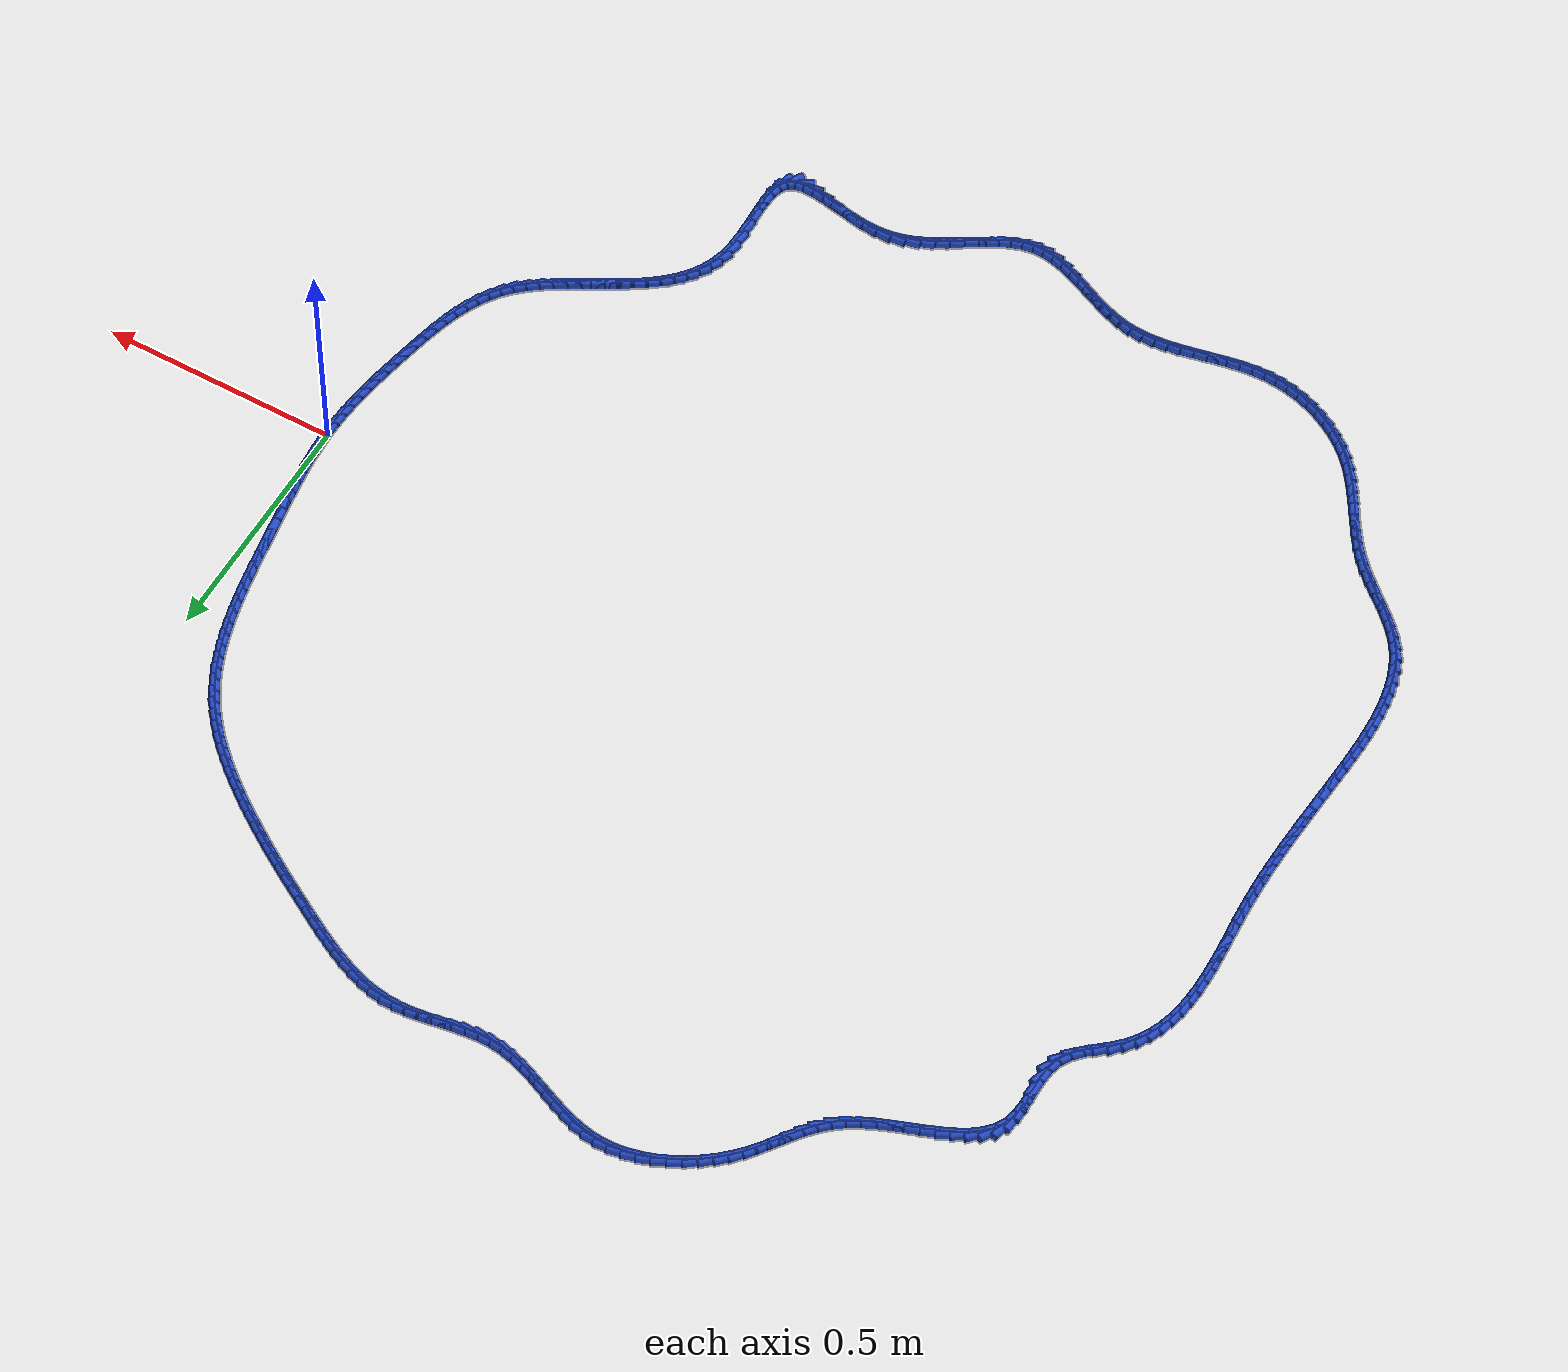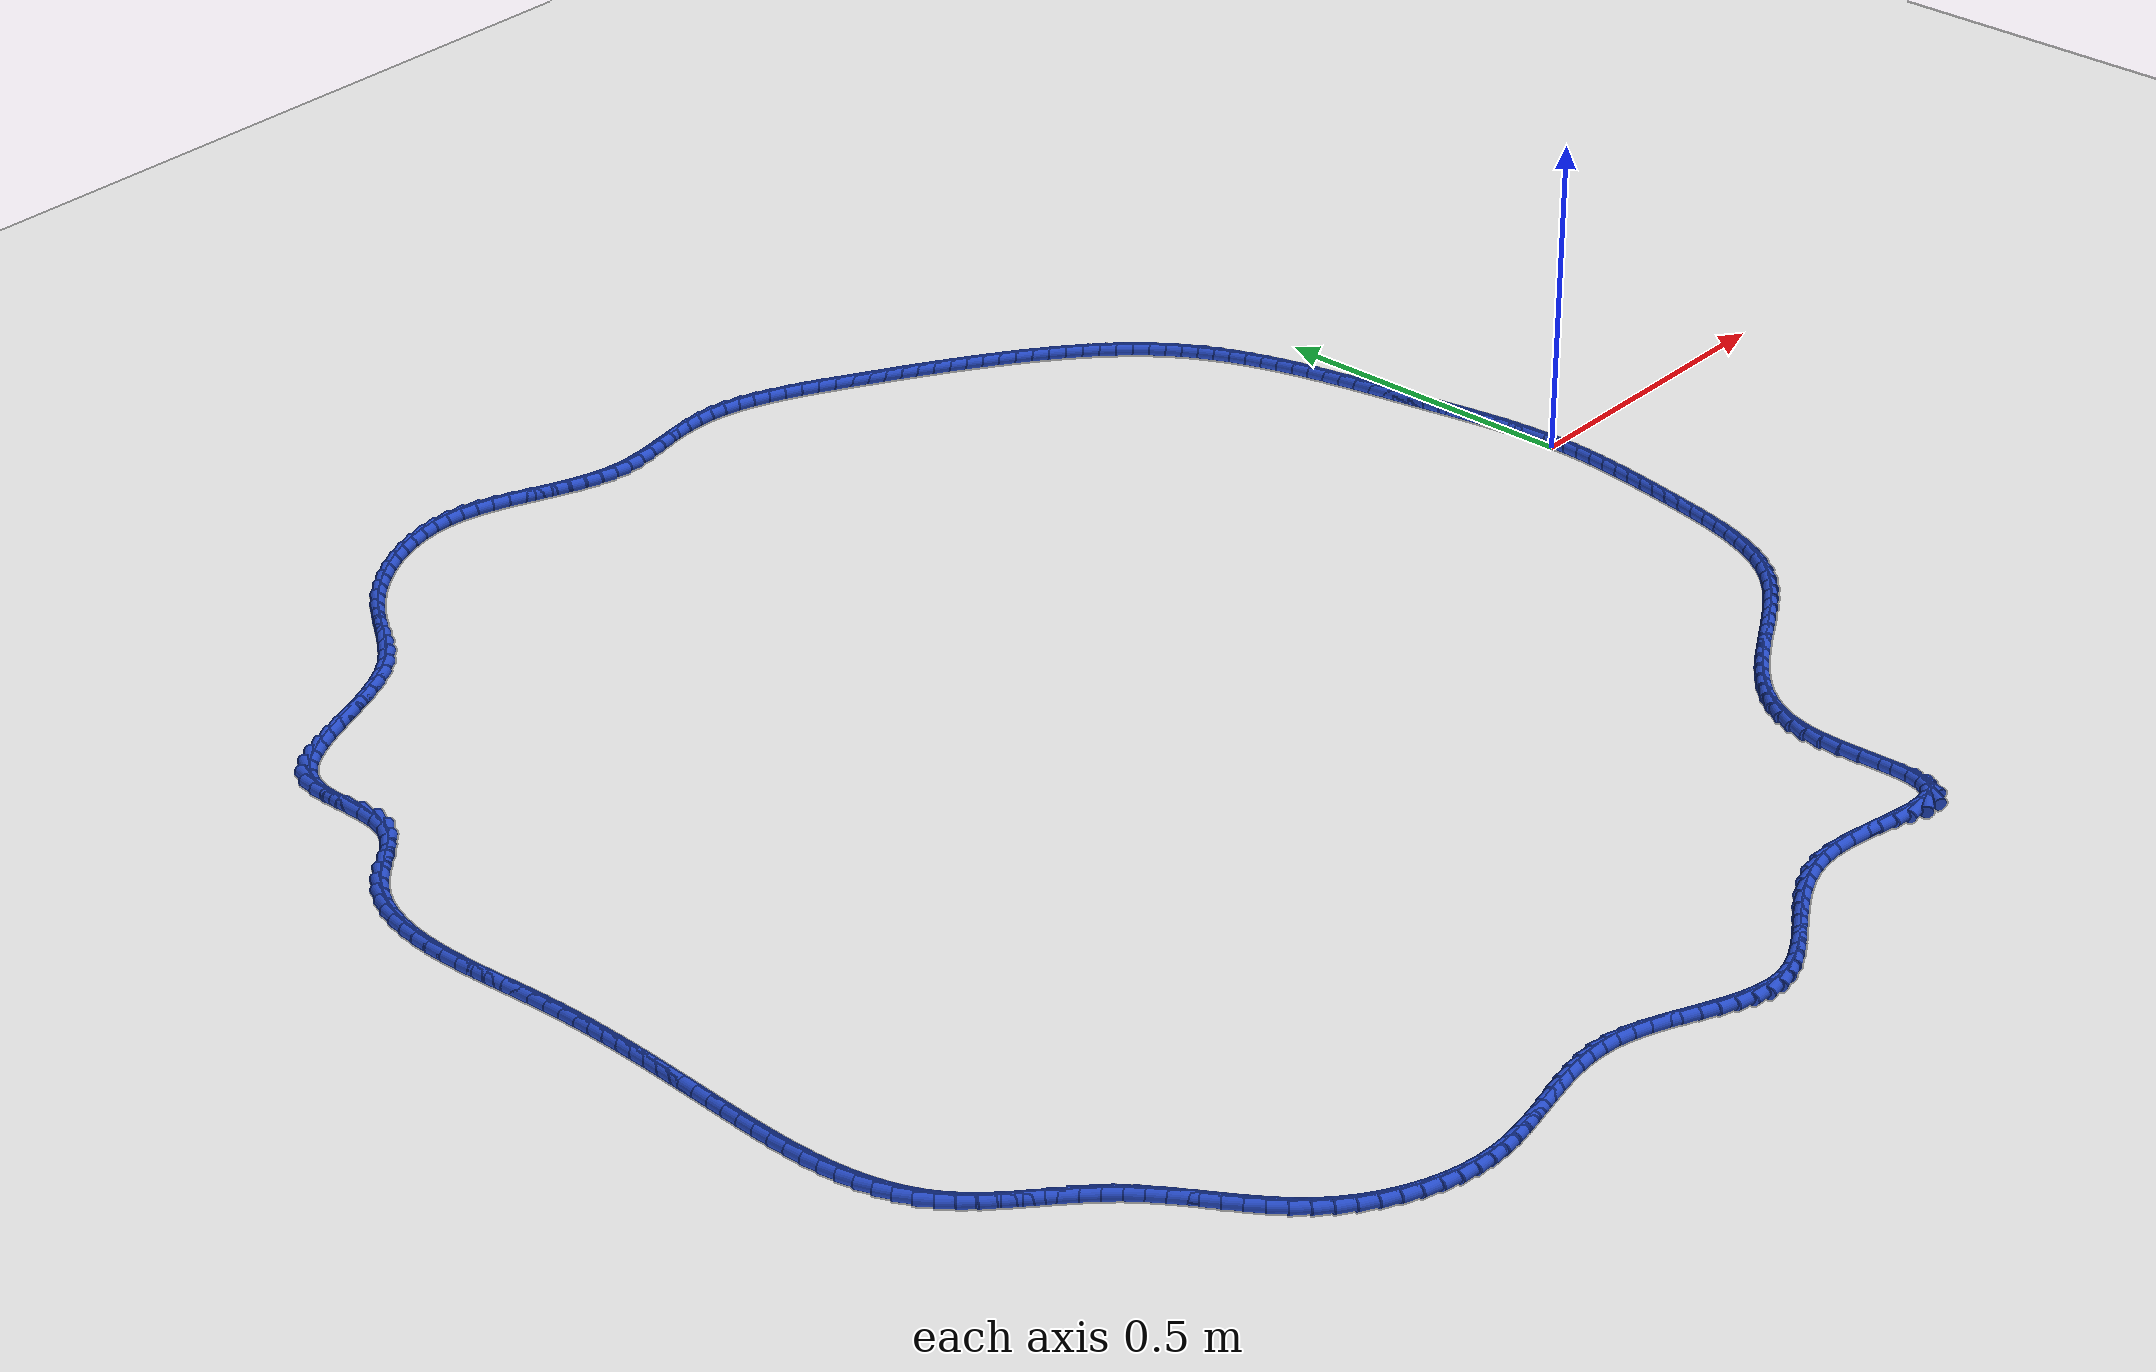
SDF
<sdf version="1.6">
 <world name="default">
  <light name="sun" type="directional">
   <pose>0 0 10 0 -0 0</pose>
   <diffuse>0.8 0.8 0.8 1</diffuse>
   <specular>0.2 0.2 0.2 1</specular>
   <attenuation>
    <range>1000</range>
    <constant>0.9</constant>
    <linear>0.01</linear>
    <quadratic>0.001</quadratic>
   </attenuation>
   <direction>-0.5 0.1 -0.9</direction>
  </light>
  <model name="ground_plane">
   <static>1</static>
   <link name="link">
    <collision name="collision">
     <geometry><plane><normal>0 0 1</normal><size>100 100</size></plane></geometry>
     <surface><friction><ode><mu>100</mu><mu2>50</mu2></ode></friction></surface>
    </collision>
    <visual name="visual">
     <cast_shadows>0</cast_shadows>
     <geometry><plane><normal>0 0 1</normal><size>100 100</size></plane></geometry>
     <material>
      <script><uri>file://media/materials/scripts/gazebo.material</uri><name>Gazebo/WhiteGlow</name></script>
     </material>
    </visual>
   </link>
  </model>
  <gravity>0 0 -9.8</gravity>
  <magnetic_field>6e-06 2.3e-05 -4.2e-05</magnetic_field>
  <atmosphere type="adiabatic"/>
  <physics name="default_physics" default="0" type="ode">
   <max_step_size>0.001</max_step_size>
   <real_time_factor>1</real_time_factor>
   <real_time_update_rate>1000</real_time_update_rate>
  </physics>
  <scene><ambient>0.4 0.4 0.4 1</ambient><background>0.7 0.7 0.7 1</background><shadows>1</shadows></scene>
  <spherical_coordinates>
   <surface_model>EARTH_WGS84</surface_model>
   <latitude_deg>0</latitude_deg>
   <longitude_deg>0</longitude_deg>
   <elevation>0</elevation>
   <heading_deg>0</heading_deg>
  </spherical_coordinates>
  <model name="line">
   <link name="link_0">
    <pose>2.6020852139652106e-18 2.7755575615628914e-17 0.01 0 1.57 -1.5447094421264198</pose>
    <collision name="collision">
     <geometry><cylinder><radius>0.01</radius><length>0.08</length></cylinder></geometry>
    </collision>
    <visual name="visual">
     <material>
      <script><name>Gazebo/Blue</name><uri>file://media/materials/scripts/gazebo.material</uri></script>
     </material>
     <geometry><cylinder><radius>0.01</radius><length>0.08</length></cylinder></geometry>
    </visual>
   </link>
   <link name="link_1">
    <pose>-0.0006769524643260038 0.025944029147597688 0.01 0 1.57 -1.5100900439261125</pose>
    <collision name="collision">
     <geometry><cylinder><radius>0.01</radius><length>0.08</length></cylinder></geometry>
    </collision>
    <visual name="visual">
     <material>
      <script><name>Gazebo/Blue</name><uri>file://media/materials/scripts/gazebo.material</uri></script>
     </material>
     <geometry><cylinder><radius>0.01</radius><length>0.08</length></cylinder></geometry>
    </visual>
   </link>
   <link name="link_2">
    <pose>-0.002255354939390575 0.05191272607095028 0.01 0 1.57 -1.4803244715710675</pose>
    <collision name="collision">
     <geometry><cylinder><radius>0.01</radius><length>0.08</length></cylinder></geometry>
    </collision>
    <visual name="visual">
     <material>
      <script><name>Gazebo/Blue</name><uri>file://media/materials/scripts/gazebo.material</uri></script>
     </material>
     <geometry><cylinder><radius>0.01</radius><length>0.08</length></cylinder></geometry>
    </visual>
   </link>
   <link name="link_3">
    <pose>-0.004614749920993577 0.07792030733704819 0.01 0 1.57 -1.4554301864849306</pose>
    <collision name="collision">
     <geometry><cylinder><radius>0.01</radius><length>0.08</length></cylinder></geometry>
    </collision>
    <visual name="visual">
     <material>
      <script><name>Gazebo/Blue</name><uri>file://media/materials/scripts/gazebo.material</uri></script>
     </material>
     <geometry><cylinder><radius>0.01</radius><length>0.08</length></cylinder></geometry>
    </visual>
   </link>
   <link name="link_4">
    <pose>-0.007634679904934878 0.10398098951288173 0.01 0 1.57 -1.435377638917283</pose>
    <collision name="collision">
     <geometry><cylinder><radius>0.01</radius><length>0.08</length></cylinder></geometry>
    </collision>
    <visual name="visual">
     <material>
      <script><name>Gazebo/Blue</name><uri>file://media/materials/scripts/gazebo.material</uri></script>
     </material>
     <geometry><cylinder><radius>0.01</radius><length>0.08</length></cylinder></geometry>
    </visual>
   </link>
   <link name="link_5">
    <pose>-0.011194687387014351 0.1301089891654413 0.01 0 1.57 -1.420108404458254</pose>
    <collision name="collision">
     <geometry><cylinder><radius>0.01</radius><length>0.08</length></cylinder></geometry>
    </collision>
    <visual name="visual">
     <material>
      <script><name>Gazebo/Blue</name><uri>file://media/materials/scripts/gazebo.material</uri></script>
     </material>
     <geometry><cylinder><radius>0.01</radius><length>0.08</length></cylinder></geometry>
    </visual>
   </link>
   <link name="link_6">
    <pose>-0.015174314863031862 0.15631852286171719 0.01 0 1.57 -1.409549563930252</pose>
    <collision name="collision">
     <geometry><cylinder><radius>0.01</radius><length>0.08</length></cylinder></geometry>
    </collision>
    <visual name="visual">
     <material>
      <script><name>Gazebo/Blue</name><uri>file://media/materials/scripts/gazebo.material</uri></script>
     </material>
     <geometry><cylinder><radius>0.01</radius><length>0.08</length></cylinder></geometry>
    </visual>
   </link>
   <link name="link_7">
    <pose>-0.019453104828787288 0.18262380716869986 0.01 0 1.57 -1.4036242079029975</pose>
    <collision name="collision">
     <geometry><cylinder><radius>0.01</radius><length>0.08</length></cylinder></geometry>
    </collision>
    <visual name="visual">
     <material>
      <script><name>Gazebo/Blue</name><uri>file://media/materials/scripts/gazebo.material</uri></script>
     </material>
     <geometry><cylinder><radius>0.01</radius><length>0.08</length></cylinder></geometry>
    </visual>
   </link>
   <link name="link_8">
    <pose>-0.023910599780080498 0.2090390586533796 0.01 0 1.57 -1.4022582798342151</pose>
    <collision name="collision">
     <geometry><cylinder><radius>0.01</radius><length>0.08</length></cylinder></geometry>
    </collision>
    <visual name="visual">
     <material>
      <script><name>Gazebo/Blue</name><uri>file://media/materials/scripts/gazebo.material</uri></script>
     </material>
     <geometry><cylinder><radius>0.01</radius><length>0.08</length></cylinder></geometry>
    </visual>
   </link>
   <link name="link_9">
    <pose>-0.028426342212711356 0.23557849388274674 0.01 0 1.57 -1.404509090377896</pose>
    <collision name="collision">
     <geometry><cylinder><radius>0.01</radius><length>0.08</length></cylinder></geometry>
    </collision>
    <visual name="visual">
     <material>
      <script><name>Gazebo/Blue</name><uri>file://media/materials/scripts/gazebo.material</uri></script>
     </material>
     <geometry><cylinder><radius>0.01</radius><length>0.08</length></cylinder></geometry>
    </visual>
   </link>
   <link name="link_10">
    <pose>-0.032902531148956984 0.2622483398547428 0.01 0 1.57 -1.4049930176146386</pose>
    <collision name="collision">
     <geometry><cylinder><radius>0.01</radius><length>0.08</length></cylinder></geometry>
    </collision>
    <visual name="visual">
     <material>
      <script><name>Gazebo/Blue</name><uri>file://media/materials/scripts/gazebo.material</uri></script>
     </material>
     <geometry><cylinder><radius>0.01</radius><length>0.08</length></cylinder></geometry>
    </visual>
   </link>
   <link name="link_11">
    <pose>-0.0373801278206156 0.2890058906359765 0.01 0 1.57 -1.4017098681388058</pose>
    <collision name="collision">
     <geometry><cylinder><radius>0.01</radius><length>0.08</length></cylinder></geometry>
    </collision>
    <visual name="visual">
     <material>
      <script><name>Gazebo/Blue</name><uri>file://media/materials/scripts/gazebo.material</uri></script>
     </material>
     <geometry><cylinder><radius>0.01</radius><length>0.08</length></cylinder></geometry>
    </visual>
   </link>
   <link name="link_12">
    <pose>-0.04195260432512614 0.31578992292733105 0.01 0 1.57 -1.3946572514319164</pose>
    <collision name="collision">
     <geometry><cylinder><radius>0.01</radius><length>0.08</length></cylinder></geometry>
    </collision>
    <visual name="visual">
     <material>
      <script><name>Gazebo/Blue</name><uri>file://media/materials/scripts/gazebo.material</uri></script>
     </material>
     <geometry><cylinder><radius>0.01</radius><length>0.08</length></cylinder></geometry>
    </visual>
   </link>
   <link name="link_13">
    <pose>-0.04671353150580254 0.3425391786080681 0.01 0 1.57 -1.383800849583464</pose>
    <collision name="collision">
     <geometry><cylinder><radius>0.01</radius><length>0.08</length></cylinder></geometry>
    </collision>
    <visual name="visual">
     <material>
      <script><name>Gazebo/Blue</name><uri>file://media/materials/scripts/gazebo.material</uri></script>
     </material>
     <geometry><cylinder><radius>0.01</radius><length>0.08</length></cylinder></geometry>
    </visual>
   </link>
   <link name="link_14">
    <pose>-0.051756480205958785 0.3691923995574494 0.01 0 1.57 -1.369073128355578</pose>
    <collision name="collision">
     <geometry><cylinder><radius>0.01</radius><length>0.08</length></cylinder></geometry>
    </collision>
    <visual name="visual">
     <material>
      <script><name>Gazebo/Blue</name><uri>file://media/materials/scripts/gazebo.material</uri></script>
     </material>
     <geometry><cylinder><radius>0.01</radius><length>0.08</length></cylinder></geometry>
    </visual>
   </link>
   <link name="link_15">
    <pose>-0.05717502126890887 0.3956883276547368 0.01 0 1.57 -1.350376945615379</pose>
    <collision name="collision">
     <geometry><cylinder><radius>0.01</radius><length>0.08</length></cylinder></geometry>
    </collision>
    <visual name="visual">
     <material>
      <script><name>Gazebo/Blue</name><uri>file://media/materials/scripts/gazebo.material</uri></script>
     </material>
     <geometry><cylinder><radius>0.01</radius><length>0.08</length></cylinder></geometry>
    </visual>
   </link>
   <link name="link_16">
    <pose>-0.0630627255379667 0.4219657047791917 0.01 0 1.57 -1.3275906923907972</pose>
    <collision name="collision">
     <geometry><cylinder><radius>0.01</radius><length>0.08</length></cylinder></geometry>
    </collision>
    <visual name="visual">
     <material>
      <script><name>Gazebo/Blue</name><uri>file://media/materials/scripts/gazebo.material</uri></script>
     </material>
     <geometry><cylinder><radius>0.01</radius><length>0.08</length></cylinder></geometry>
    </visual>
   </link>
   <link name="link_17">
    <pose>-0.0695131638564463 0.4479632728100762 0.01 0 1.57 -1.3005755761587714</pose>
    <collision name="collision">
     <geometry><cylinder><radius>0.01</radius><length>0.08</length></cylinder></geometry>
    </collision>
    <visual name="visual">
     <material>
      <script><name>Gazebo/Blue</name><uri>file://media/materials/scripts/gazebo.material</uri></script>
     </material>
     <geometry><cylinder><radius>0.01</radius><length>0.08</length></cylinder></geometry>
    </visual>
   </link>
   <link name="link_18">
    <pose>-0.07661990706766159 0.47361977362665153 0.01 0 1.57 -1.2691857881140747</pose>
    <collision name="collision">
     <geometry><cylinder><radius>0.01</radius><length>0.08</length></cylinder></geometry>
    </collision>
    <visual name="visual">
     <material>
      <script><name>Gazebo/Blue</name><uri>file://media/materials/scripts/gazebo.material</uri></script>
     </material>
     <geometry><cylinder><radius>0.01</radius><length>0.08</length></cylinder></geometry>
    </visual>
   </link>
   <link name="link_19">
    <pose>-0.0844765260149266 0.49887394910818 0.01 0 1.57 -1.2332823554020298</pose>
    <collision name="collision">
     <geometry><cylinder><radius>0.01</radius><length>0.08</length></cylinder></geometry>
    </collision>
    <visual name="visual">
     <material>
      <script><name>Gazebo/Blue</name><uri>file://media/materials/scripts/gazebo.material</uri></script>
     </material>
     <geometry><cylinder><radius>0.01</radius><length>0.08</length></cylinder></geometry>
    </visual>
   </link>
   <link name="link_20">
    <pose>-0.09317659154155523 0.5236645411339228 0.01 0 1.57 -1.1927513883036622</pose>
    <collision name="collision">
     <geometry><cylinder><radius>0.01</radius><length>0.08</length></cylinder></geometry>
    </collision>
    <visual name="visual">
     <material>
      <script><name>Gazebo/Blue</name><uri>file://media/materials/scripts/gazebo.material</uri></script>
     </material>
     <geometry><cylinder><radius>0.01</radius><length>0.08</length></cylinder></geometry>
    </visual>
   </link>
   <link name="link_21">
    <pose>-0.1028136744908615 0.547930291583142 0.01 0 1.57 -1.1475270799617239</pose>
    <collision name="collision">
     <geometry><cylinder><radius>0.01</radius><length>0.08</length></cylinder></geometry>
    </collision>
    <visual name="visual">
     <material>
      <script><name>Gazebo/Blue</name><uri>file://media/materials/scripts/gazebo.material</uri></script>
     </material>
     <geometry><cylinder><radius>0.01</radius><length>0.08</length></cylinder></geometry>
    </visual>
   </link>
   <link name="link_22">
    <pose>-0.11348134570615934 0.571609942335099 0.01 0 1.57 -1.0976190742251068</pose>
    <collision name="collision">
     <geometry><cylinder><radius>0.01</radius><length>0.08</length></cylinder></geometry>
    </collision>
    <visual name="visual">
     <material>
      <script><name>Gazebo/Blue</name><uri>file://media/materials/scripts/gazebo.material</uri></script>
     </material>
     <geometry><cylinder><radius>0.01</radius><length>0.08</length></cylinder></geometry>
    </visual>
   </link>
   <link name="link_23">
    <pose>-0.12527317603076274 0.5946422352690558 0.01 0 1.57 -1.0431425920916884</pose>
    <collision name="collision">
     <geometry><cylinder><radius>0.01</radius><length>0.08</length></cylinder></geometry>
    </collision>
    <visual name="visual">
     <material>
      <script><name>Gazebo/Blue</name><uri>file://media/materials/scripts/gazebo.material</uri></script>
     </material>
     <geometry><cylinder><radius>0.01</radius><length>0.08</length></cylinder></geometry>
    </visual>
   </link>
   <link name="link_24">
    <pose>-0.1382827363079857 0.6169659122642741 0.01 0 1.57 -0.984368553700614</pose>
    <collision name="collision">
     <geometry><cylinder><radius>0.01</radius><length>0.08</length></cylinder></geometry>
    </collision>
    <visual name="visual">
     <material>
      <script><name>Gazebo/Blue</name><uri>file://media/materials/scripts/gazebo.material</uri></script>
     </material>
     <geometry><cylinder><radius>0.01</radius><length>0.08</length></cylinder></geometry>
    </visual>
   </link>
   <link name="link_25">
    <pose>-0.15260310255913614 0.6385199297352661 0.01 0 1.57 -0.924508777456821</pose>
    <collision name="collision">
     <geometry><cylinder><radius>0.01</radius><length>0.08</length></cylinder></geometry>
    </collision>
    <visual name="visual">
     <material>
      <script><name>Gazebo/Blue</name><uri>file://media/materials/scripts/gazebo.material</uri></script>
     </material>
     <geometry><cylinder><radius>0.01</radius><length>0.08</length></cylinder></geometry>
    </visual>
   </link>
   <link name="link_26">
    <pose>-0.16825851615281318 0.6592730880794121 0.01 0 1.57 -0.8694539486937449</pose>
    <collision name="collision">
     <geometry><cylinder><radius>0.01</radius><length>0.08</length></cylinder></geometry>
    </collision>
    <visual name="visual">
     <material>
      <script><name>Gazebo/Blue</name><uri>file://media/materials/scripts/gazebo.material</uri></script>
     </material>
     <geometry><cylinder><radius>0.01</radius><length>0.08</length></cylinder></geometry>
    </visual>
   </link>
   <link name="link_27">
    <pose>-0.1851344179754364 0.6792543660933328 0.01 0 1.57 -0.8197957248820276</pose>
    <collision name="collision">
     <geometry><cylinder><radius>0.01</radius><length>0.08</length></cylinder></geometry>
    </collision>
    <visual name="visual">
     <material>
      <script><name>Gazebo/Blue</name><uri>file://media/materials/scripts/gazebo.material</uri></script>
     </material>
     <geometry><cylinder><radius>0.01</radius><length>0.08</length></cylinder></geometry>
    </visual>
   </link>
   <link name="link_28">
    <pose>-0.20309956402799006 0.6984999764800532 0.01 0 1.57 -0.7753371779194762</pose>
    <collision name="collision">
     <geometry><cylinder><radius>0.01</radius><length>0.08</length></cylinder></geometry>
    </collision>
    <visual name="visual">
     <material>
      <script><name>Gazebo/Blue</name><uri>file://media/materials/scripts/gazebo.material</uri></script>
     </material>
     <geometry><cylinder><radius>0.01</radius><length>0.08</length></cylinder></geometry>
    </visual>
   </link>
   <link name="link_29">
    <pose>-0.22202271031145848 0.7170461319425983 0.01 0 1.57 -0.7358281324362274</pose>
    <collision name="collision">
     <geometry><cylinder><radius>0.01</radius><length>0.08</length></cylinder></geometry>
    </collision>
    <visual name="visual">
     <material>
      <script><name>Gazebo/Blue</name><uri>file://media/materials/scripts/gazebo.material</uri></script>
     </material>
     <geometry><cylinder><radius>0.01</radius><length>0.08</length></cylinder></geometry>
    </visual>
   </link>
   <link name="link_30">
    <pose>-0.24177261282682586 0.7349290451839929 0.01 0 1.57 -0.7009991020640058</pose>
    <collision name="collision">
     <geometry><cylinder><radius>0.01</radius><length>0.08</length></cylinder></geometry>
    </collision>
    <visual name="visual">
     <material>
      <script><name>Gazebo/Blue</name><uri>file://media/materials/scripts/gazebo.material</uri></script>
     </material>
     <geometry><cylinder><radius>0.01</radius><length>0.08</length></cylinder></geometry>
    </visual>
   </link>
   <link name="link_31">
    <pose>-0.2622180275750764 0.7521849289072624 0.01 0 1.57 -0.6705862700640924</pose>
    <collision name="collision">
     <geometry><cylinder><radius>0.01</radius><length>0.08</length></cylinder></geometry>
    </collision>
    <visual name="visual">
     <material>
      <script><name>Gazebo/Blue</name><uri>file://media/materials/scripts/gazebo.material</uri></script>
     </material>
     <geometry><cylinder><radius>0.01</radius><length>0.08</length></cylinder></geometry>
    </visual>
   </link>
   <link name="link_32">
    <pose>-0.2832277105571945 0.7688499958154315 0.01 0 1.57 -0.64434918952249</pose>
    <collision name="collision">
     <geometry><cylinder><radius>0.01</radius><length>0.08</length></cylinder></geometry>
    </collision>
    <visual name="visual">
     <material>
      <script><name>Gazebo/Blue</name><uri>file://media/materials/scripts/gazebo.material</uri></script>
     </material>
     <geometry><cylinder><radius>0.01</radius><length>0.08</length></cylinder></geometry>
    </visual>
   </link>
   <link name="link_33">
    <pose>-0.3046704177741643 0.7849604586115251 0.01 0 1.57 -0.6220831686011091</pose>
    <collision name="collision">
     <geometry><cylinder><radius>0.01</radius><length>0.08</length></cylinder></geometry>
    </collision>
    <visual name="visual">
     <material>
      <script><name>Gazebo/Blue</name><uri>file://media/materials/scripts/gazebo.material</uri></script>
     </material>
     <geometry><cylinder><radius>0.01</radius><length>0.08</length></cylinder></geometry>
    </visual>
   </link>
   <link name="link_34">
    <pose>-0.3264149052269702 0.8005525299985685 0.01 0 1.57 -0.6036259810245913</pose>
    <collision name="collision">
     <geometry><cylinder><radius>0.01</radius><length>0.08</length></cylinder></geometry>
    </collision>
    <visual name="visual">
     <material>
      <script><name>Gazebo/Blue</name><uri>file://media/materials/scripts/gazebo.material</uri></script>
     </material>
     <geometry><cylinder><radius>0.01</radius><length>0.08</length></cylinder></geometry>
    </visual>
   </link>
   <link name="link_35">
    <pose>-0.34833005311608584 0.8156624364001636 0.01 0 1.57 -0.5881525538069565</pose>
    <collision name="collision">
     <geometry><cylinder><radius>0.01</radius><length>0.08</length></cylinder></geometry>
    </collision>
    <visual name="visual">
     <material>
      <script><name>Gazebo/Blue</name><uri>file://media/materials/scripts/gazebo.material</uri></script>
     </material>
     <geometry><cylinder><radius>0.01</radius><length>0.08</length></cylinder></geometry>
    </visual>
   </link>
   <link name="link_36">
    <pose>-0.3703256341965933 0.8303309217257456 0.01 0 1.57 -0.573928437207423</pose>
    <collision name="collision">
     <geometry><cylinder><radius>0.01</radius><length>0.08</length></cylinder></geometry>
    </collision>
    <visual name="visual">
     <material>
      <script><name>Gazebo/Blue</name><uri>file://media/materials/scripts/gazebo.material</uri></script>
     </material>
     <geometry><cylinder><radius>0.01</radius><length>0.08</length></cylinder></geometry>
    </visual>
   </link>
   <link name="link_37">
    <pose>-0.39241112752740775 0.8446097446481814 0.01 0 1.57 -0.5607891031118247</pose>
    <collision name="collision">
     <geometry><cylinder><radius>0.01</radius><length>0.08</length></cylinder></geometry>
    </collision>
    <visual name="visual">
     <material>
      <script><name>Gazebo/Blue</name><uri>file://media/materials/scripts/gazebo.material</uri></script>
     </material>
     <geometry><cylinder><radius>0.01</radius><length>0.08</length></cylinder></geometry>
    </visual>
   </link>
   <link name="link_38">
    <pose>-0.4146109215787564 0.858552310914116 0.01 0 1.57 -0.548823795246978</pose>
    <collision name="collision">
     <geometry><cylinder><radius>0.01</radius><length>0.08</length></cylinder></geometry>
    </collision>
    <visual name="visual">
     <material>
      <script><name>Gazebo/Blue</name><uri>file://media/materials/scripts/gazebo.material</uri></script>
     </material>
     <geometry><cylinder><radius>0.01</radius><length>0.08</length></cylinder></geometry>
    </visual>
   </link>
   <link name="link_39">
    <pose>-0.43694940482086586 0.8722120262701932 0.01 0 1.57 -0.5381071029037967</pose>
    <collision name="collision">
     <geometry><cylinder><radius>0.01</radius><length>0.08</length></cylinder></geometry>
    </collision>
    <visual name="visual">
     <material>
      <script><name>Gazebo/Blue</name><uri>file://media/materials/scripts/gazebo.material</uri></script>
     </material>
     <geometry><cylinder><radius>0.01</radius><length>0.08</length></cylinder></geometry>
    </visual>
   </link>
   <link name="link_40">
    <pose>-0.45945096572396293 0.8856422964630577 0.01 0 1.57 -0.528697873519467</pose>
    <collision name="collision">
     <geometry><cylinder><radius>0.01</radius><length>0.08</length></cylinder></geometry>
    </collision>
    <visual name="visual">
     <material>
      <script><name>Gazebo/Blue</name><uri>file://media/materials/scripts/gazebo.material</uri></script>
     </material>
     <geometry><cylinder><radius>0.01</radius><length>0.08</length></cylinder></geometry>
    </visual>
   </link>
   <link name="link_41">
    <pose>-0.48213999275827485 0.8988965272393539 0.01 0 1.57 -0.5206386159855023</pose>
    <collision name="collision">
     <geometry><cylinder><radius>0.01</radius><length>0.08</length></cylinder></geometry>
    </collision>
    <visual name="visual">
     <material>
      <script><name>Gazebo/Blue</name><uri>file://media/materials/scripts/gazebo.material</uri></script>
     </material>
     <geometry><cylinder><radius>0.01</radius><length>0.08</length></cylinder></geometry>
    </visual>
   </link>
   <link name="link_42">
    <pose>-0.5050408743940286 0.912028124345726 0.01 0 1.57 -0.5139553764786593</pose>
    <collision name="collision">
     <geometry><cylinder><radius>0.01</radius><length>0.08</length></cylinder></geometry>
    </collision>
    <visual name="visual">
     <material>
      <script><name>Gazebo/Blue</name><uri>file://media/materials/scripts/gazebo.material</uri></script>
     </material>
     <geometry><cylinder><radius>0.01</radius><length>0.08</length></cylinder></geometry>
    </visual>
   </link>
   <link name="link_43">
    <pose>-0.528177999101451 0.9250904935288189 0.01 0 1.57 -0.5086580471919975</pose>
    <collision name="collision">
     <geometry><cylinder><radius>0.01</radius><length>0.08</length></cylinder></geometry>
    </collision>
    <visual name="visual">
     <material>
      <script><name>Gazebo/Blue</name><uri>file://media/materials/scripts/gazebo.material</uri></script>
     </material>
     <geometry><cylinder><radius>0.01</radius><length>0.08</length></cylinder></geometry>
    </visual>
   </link>
   <link name="link_44">
    <pose>-0.5515757553507691 0.9381370405352767 0.01 0 1.57 -0.5034489246326013</pose>
    <collision name="collision">
     <geometry><cylinder><radius>0.01</radius><length>0.08</length></cylinder></geometry>
    </collision>
    <visual name="visual">
     <material>
      <script><name>Gazebo/Blue</name><uri>file://media/materials/scripts/gazebo.material</uri></script>
     </material>
     <geometry><cylinder><radius>0.01</radius><length>0.08</length></cylinder></geometry>
    </visual>
   </link>
   <link name="link_45">
    <pose>-0.5752548627448204 0.9511792372746727 0.01 0 1.57 -0.4913635665854086</pose>
    <collision name="collision">
     <geometry><cylinder><radius>0.01</radius><length>0.08</length></cylinder></geometry>
    </collision>
    <visual name="visual">
     <material>
      <script><name>Gazebo/Blue</name><uri>file://media/materials/scripts/gazebo.material</uri></script>
     </material>
     <geometry><cylinder><radius>0.01</radius><length>0.08</length></cylinder></geometry>
    </visual>
   </link>
   <link name="link_46">
    <pose>-0.5992162135918869 0.9640019367981443 0.01 0 1.57 -0.46999554203275534</pose>
    <collision name="collision">
     <geometry><cylinder><radius>0.01</radius><length>0.08</length></cylinder></geometry>
    </collision>
    <visual name="visual">
     <material>
      <script><name>Gazebo/Blue</name><uri>file://media/materials/scripts/gazebo.material</uri></script>
     </material>
     <geometry><cylinder><radius>0.01</radius><length>0.08</length></cylinder></geometry>
    </visual>
   </link>
   <link name="link_47">
    <pose>-0.6234540328256201 0.9763137864585127 0.01 0 1.57 -0.43904641459854177</pose>
    <collision name="collision">
     <geometry><cylinder><radius>0.01</radius><length>0.08</length></cylinder></geometry>
    </collision>
    <visual name="visual">
     <material>
      <script><name>Gazebo/Blue</name><uri>file://media/materials/scripts/gazebo.material</uri></script>
     </material>
     <geometry><cylinder><radius>0.01</radius><length>0.08</length></cylinder></geometry>
    </visual>
   </link>
   <link name="link_48">
    <pose>-0.6479625403933298 0.9878233766165061 0.01 0 1.57 -0.39800833734970154</pose>
    <collision name="collision">
     <geometry><cylinder><radius>0.01</radius><length>0.08</length></cylinder></geometry>
    </collision>
    <visual name="visual">
     <material>
      <script><name>Gazebo/Blue</name><uri>file://media/materials/scripts/gazebo.material</uri></script>
     </material>
     <geometry><cylinder><radius>0.01</radius><length>0.08</length></cylinder></geometry>
    </visual>
   </link>
   <link name="link_49">
    <pose>-0.6727359562423264 0.9982392976328537 0.01 0 1.57 -0.34623181460450403</pose>
    <collision name="collision">
     <geometry><cylinder><radius>0.01</radius><length>0.08</length></cylinder></geometry>
    </collision>
    <visual name="visual">
     <material>
      <script><name>Gazebo/Blue</name><uri>file://media/materials/scripts/gazebo.material</uri></script>
     </material>
     <geometry><cylinder><radius>0.01</radius><length>0.08</length></cylinder></geometry>
    </visual>
   </link>
   <link name="link_50">
    <pose>-0.6977685003199204 1.007270139868284 0.01 0 1.57 -0.28303955580473206</pose>
    <collision name="collision">
     <geometry><cylinder><radius>0.01</radius><length>0.08</length></cylinder></geometry>
    </collision>
    <visual name="visual">
     <material>
      <script><name>Gazebo/Blue</name><uri>file://media/materials/scripts/gazebo.material</uri></script>
     </material>
     <geometry><cylinder><radius>0.01</radius><length>0.08</length></cylinder></geometry>
    </visual>
   </link>
   <link name="link_51">
    <pose>-0.7230543925734221 1.014624493683526 0.01 0 1.57 -0.20790835478851716</pose>
    <collision name="collision">
     <geometry><cylinder><radius>0.01</radius><length>0.08</length></cylinder></geometry>
    </collision>
    <visual name="visual">
     <material>
      <script><name>Gazebo/Blue</name><uri>file://media/materials/scripts/gazebo.material</uri></script>
     </material>
     <geometry><cylinder><radius>0.01</radius><length>0.08</length></cylinder></geometry>
    </visual>
   </link>
   <link name="link_52">
    <pose>-0.7485878529501413 1.0200109494393088 0.01 0 1.57 -0.1207336129618366</pose>
    <collision name="collision">
     <geometry><cylinder><radius>0.01</radius><length>0.08</length></cylinder></geometry>
    </collision>
    <visual name="visual">
     <material>
      <script><name>Gazebo/Blue</name><uri>file://media/materials/scripts/gazebo.material</uri></script>
     </material>
     <geometry><cylinder><radius>0.01</radius><length>0.08</length></cylinder></geometry>
    </visual>
   </link>
   <link name="link_53">
    <pose>-0.7743631013973884 1.0231380974963606 0.01 0 1.57 -0.022465557204322025</pose>
    <collision name="collision">
     <geometry><cylinder><radius>0.01</radius><length>0.08</length></cylinder></geometry>
    </collision>
    <visual name="visual">
     <material>
      <script><name>Gazebo/Blue</name><uri>file://media/materials/scripts/gazebo.material</uri></script>
     </material>
     <geometry><cylinder><radius>0.01</radius><length>0.08</length></cylinder></geometry>
    </visual>
   </link>
   <link name="link_54">
    <pose>-0.8003738665643457 1.0237225421557743 0.01 0 1.57 0.06960390742089367</pose>
    <collision name="collision">
     <geometry><cylinder><radius>0.01</radius><length>0.08</length></cylinder></geometry>
    </collision>
    <visual name="visual">
     <material>
      <script><name>Gazebo/Blue</name><uri>file://media/materials/scripts/gazebo.material</uri></script>
     </material>
     <geometry><cylinder><radius>0.01</radius><length>0.08</length></cylinder></geometry>
    </visual>
   </link>
   <link name="link_55">
    <pose>-0.8265884928673899 1.021894949397888 0.01 0 1.57 0.13216317321543872</pose>
    <collision name="collision">
     <geometry><cylinder><radius>0.01</radius><length>0.08</length></cylinder></geometry>
    </collision>
    <visual name="visual">
     <material>
      <script><name>Gazebo/Blue</name><uri>file://media/materials/scripts/gazebo.material</uri></script>
     </material>
     <geometry><cylinder><radius>0.01</radius><length>0.08</length></cylinder></geometry>
    </visual>
   </link>
   <link name="link_56">
    <pose>-0.8529381681911589 1.018392073874078 0.01 0 1.57 0.16481963725811485</pose>
    <collision name="collision">
     <geometry><cylinder><radius>0.01</radius><length>0.08</length></cylinder></geometry>
    </collision>
    <visual name="visual">
     <material>
      <script><name>Gazebo/Blue</name><uri>file://media/materials/scripts/gazebo.material</uri></script>
     </material>
     <geometry><cylinder><radius>0.01</radius><length>0.08</length></cylinder></geometry>
    </visual>
   </link>
   <link name="link_57">
    <pose>-0.8793511269886184 1.0139988459236557 0.01 0 1.57 0.16875413462926475</pose>
    <collision name="collision">
     <geometry><cylinder><radius>0.01</radius><length>0.08</length></cylinder></geometry>
    </collision>
    <visual name="visual">
     <material>
      <script><name>Gazebo/Blue</name><uri>file://media/materials/scripts/gazebo.material</uri></script>
     </material>
     <geometry><cylinder><radius>0.01</radius><length>0.08</length></cylinder></geometry>
    </visual>
   </link>
   <link name="link_58">
    <pose>-0.9057556037127329 1.009500195885932 0.01 0 1.57 0.14407561529840715</pose>
    <collision name="collision">
     <geometry><cylinder><radius>0.01</radius><length>0.08</length></cylinder></geometry>
    </collision>
    <visual name="visual">
     <material>
      <script><name>Gazebo/Blue</name><uri>file://media/materials/scripts/gazebo.material</uri></script>
     </material>
     <geometry><cylinder><radius>0.01</radius><length>0.08</length></cylinder></geometry>
    </visual>
   </link>
   <link name="link_59">
    <pose>-0.9320798328164681 1.0056810541002177 0.01 0 1.57 0.08972799545765953</pose>
    <collision name="collision">
     <geometry><cylinder><radius>0.01</radius><length>0.08</length></cylinder></geometry>
    </collision>
    <visual name="visual">
     <material>
      <script><name>Gazebo/Blue</name><uri>file://media/materials/scripts/gazebo.material</uri></script>
     </material>
     <geometry><cylinder><radius>0.01</radius><length>0.08</length></cylinder></geometry>
    </visual>
   </link>
   <link name="link_60">
    <pose>-0.9582520487527886 1.0033263509058234 0.01 0 1.57 0.0040593460132363444</pose>
    <collision name="collision">
     <geometry><cylinder><radius>0.01</radius><length>0.08</length></cylinder></geometry>
    </collision>
    <visual name="visual">
     <material>
      <script><name>Gazebo/Blue</name><uri>file://media/materials/scripts/gazebo.material</uri></script>
     </material>
     <geometry><cylinder><radius>0.01</radius><length>0.08</length></cylinder></geometry>
    </visual>
   </link>
   <link name="link_61">
    <pose>-0.9842004859746596 1.0032210166420603 0.01 0 1.57 -0.10936346529876916</pose>
    <collision name="collision">
     <geometry><cylinder><radius>0.01</radius><length>0.08</length></cylinder></geometry>
    </collision>
    <visual name="visual">
     <material>
      <script><name>Gazebo/Blue</name><uri>file://media/materials/scripts/gazebo.material</uri></script>
     </material>
     <geometry><cylinder><radius>0.01</radius><length>0.08</length></cylinder></geometry>
    </visual>
   </link>
   <link name="link_62">
    <pose>-1.0098641614151322 1.0060389285091464 0.01 0 1.57 -0.21470255914398292</pose>
    <collision name="collision">
     <geometry><cylinder><radius>0.01</radius><length>0.08</length></cylinder></geometry>
    </collision>
    <visual name="visual">
     <material>
      <script><name>Gazebo/Blue</name><uri>file://media/materials/scripts/gazebo.material</uri></script>
     </material>
     <geometry><cylinder><radius>0.01</radius><length>0.08</length></cylinder></geometry>
    </visual>
   </link>
   <link name="link_63">
    <pose>-1.035267104461939 1.0115783859292657 0.01 0 1.57 -0.2944523383144027</pose>
    <collision name="collision">
     <geometry><cylinder><radius>0.01</radius><length>0.08</length></cylinder></geometry>
    </collision>
    <visual name="visual">
     <material>
      <script><name>Gazebo/Blue</name><uri>file://media/materials/scripts/gazebo.material</uri></script>
     </material>
     <geometry><cylinder><radius>0.01</radius><length>0.08</length></cylinder></geometry>
    </visual>
   </link>
   <link name="link_64">
    <pose>-1.060473634797425 1.0192227222262402 0.01 0 1.57 -0.3491933220874344</pose>
    <collision name="collision">
     <geometry><cylinder><radius>0.01</radius><length>0.08</length></cylinder></geometry>
    </collision>
    <visual name="visual">
     <material>
      <script><name>Gazebo/Blue</name><uri>file://media/materials/scripts/gazebo.material</uri></script>
     </material>
     <geometry><cylinder><radius>0.01</radius><length>0.08</length></cylinder></geometry>
    </visual>
   </link>
   <link name="link_65">
    <pose>-1.0855483140318336 1.0283527790102645 0.01 0 1.57 -0.38028790479934493</pose>
    <collision name="collision">
     <geometry><cylinder><radius>0.01</radius><length>0.08</length></cylinder></geometry>
    </collision>
    <visual name="visual">
     <material>
      <script><name>Gazebo/Blue</name><uri>file://media/materials/scripts/gazebo.material</uri></script>
     </material>
     <geometry><cylinder><radius>0.01</radius><length>0.08</length></cylinder></geometry>
    </visual>
   </link>
   <link name="link_66">
    <pose>-1.1105557037754084 1.038349397891534 0.01 0 1.57 -0.38882711111170243</pose>
    <collision name="collision">
     <geometry><cylinder><radius>0.01</radius><length>0.08</length></cylinder></geometry>
    </collision>
    <visual name="visual">
     <material>
      <script><name>Gazebo/Blue</name><uri>file://media/materials/scripts/gazebo.material</uri></script>
     </material>
     <geometry><cylinder><radius>0.01</radius><length>0.08</length></cylinder></geometry>
    </visual>
   </link>
   <link name="link_67">
    <pose>-1.1355603656383926 1.0485934204802445 0.01 0 1.57 -0.37518751675885287</pose>
    <collision name="collision">
     <geometry><cylinder><radius>0.01</radius><length>0.08</length></cylinder></geometry>
    </collision>
    <visual name="visual">
     <material>
      <script><name>Gazebo/Blue</name><uri>file://media/materials/scripts/gazebo.material</uri></script>
     </material>
     <geometry><cylinder><radius>0.01</radius><length>0.08</length></cylinder></geometry>
    </visual>
   </link>
   <link name="link_68">
    <pose>-1.160626861231029 1.0584656883865915 0.01 0 1.57 -0.33893064341563844</pose>
    <collision name="collision">
     <geometry><cylinder><radius>0.01</radius><length>0.08</length></cylinder></geometry>
    </collision>
    <visual name="visual">
     <material>
      <script><name>Gazebo/Blue</name><uri>file://media/materials/scripts/gazebo.material</uri></script>
     </material>
     <geometry><cylinder><radius>0.01</radius><length>0.08</length></cylinder></geometry>
    </visual>
   </link>
   <link name="link_69">
    <pose>-1.1858197521635612 1.0673470432207701 0.01 0 1.57 -0.2789826333580226</pose>
    <collision name="collision">
     <geometry><cylinder><radius>0.01</radius><length>0.08</length></cylinder></geometry>
    </collision>
    <visual name="visual">
     <material>
      <script><name>Gazebo/Blue</name><uri>file://media/materials/scripts/gazebo.material</uri></script>
     </material>
     <geometry><cylinder><radius>0.01</radius><length>0.08</length></cylinder></geometry>
    </visual>
   </link>
   <link name="link_70">
    <pose>-1.211203600046233 1.0746183265929763 0.01 0 1.57 -0.194175048397495</pose>
    <collision name="collision">
     <geometry><cylinder><radius>0.01</radius><length>0.08</length></cylinder></geometry>
    </collision>
    <visual name="visual">
     <material>
      <script><name>Gazebo/Blue</name><uri>file://media/materials/scripts/gazebo.material</uri></script>
     </material>
     <geometry><cylinder><radius>0.01</radius><length>0.08</length></cylinder></geometry>
    </visual>
   </link>
   <link name="link_71">
    <pose>-1.2368429664892866 1.079660380113405 0.01 0 1.57 -0.08460198125352052</pose>
    <collision name="collision">
     <geometry><cylinder><radius>0.01</radius><length>0.08</length></cylinder></geometry>
    </collision>
    <visual name="visual">
     <material>
      <script><name>Gazebo/Blue</name><uri>file://media/materials/scripts/gazebo.material</uri></script>
     </material>
     <geometry><cylinder><radius>0.01</radius><length>0.08</length></cylinder></geometry>
    </visual>
   </link>
   <link name="link_72">
    <pose>-1.2627997741751016 1.0818616317944783 0.01 0 1.57 0.03502516665725194</pose>
    <collision name="collision">
     <geometry><cylinder><radius>0.01</radius><length>0.08</length></cylinder></geometry>
    </collision>
    <visual name="visual">
     <material>
      <script><name>Gazebo/Blue</name><uri>file://media/materials/scripts/gazebo.material</uri></script>
     </material>
     <geometry><cylinder><radius>0.01</radius><length>0.08</length></cylinder></geometry>
    </visual>
   </link>
   <link name="link_73">
    <pose>-1.2890203320162057 1.080942876657463 0.01 0 1.57 0.1459978175347038</pose>
    <collision name="collision">
     <geometry><cylinder><radius>0.01</radius><length>0.08</length></cylinder></geometry>
    </collision>
    <visual name="visual">
     <material>
      <script><name>Gazebo/Blue</name><uri>file://media/materials/scripts/gazebo.material</uri></script>
     </material>
     <geometry><cylinder><radius>0.01</radius><length>0.08</length></cylinder></geometry>
    </visual>
   </link>
   <link name="link_74">
    <pose>-1.3152927600365851 1.0770796718837536 0.01 0 1.57 0.2476461349133112</pose>
    <collision name="collision">
     <geometry><cylinder><radius>0.01</radius><length>0.08</length></cylinder></geometry>
    </collision>
    <visual name="visual">
     <material>
      <script><name>Gazebo/Blue</name><uri>file://media/materials/scripts/gazebo.material</uri></script>
     </material>
     <geometry><cylinder><radius>0.01</radius><length>0.08</length></cylinder></geometry>
    </visual>
   </link>
   <link name="link_75">
    <pose>-1.341393761041711 1.0704803969281822 0.01 0 1.57 0.3411649481984167</pose>
    <collision name="collision">
     <geometry><cylinder><radius>0.01</radius><length>0.08</length></cylinder></geometry>
    </collision>
    <visual name="visual">
     <material>
      <script><name>Gazebo/Blue</name><uri>file://media/materials/scripts/gazebo.material</uri></script>
     </material>
     <geometry><cylinder><radius>0.01</radius><length>0.08</length></cylinder></geometry>
    </visual>
   </link>
   <link name="link_76">
    <pose>-1.3671000378370541 1.061353431245579 0.01 0 1.57 0.4280313531514889</pose>
    <collision name="collision">
     <geometry><cylinder><radius>0.01</radius><length>0.08</length></cylinder></geometry>
    </collision>
    <visual name="visual">
     <material>
      <script><name>Gazebo/Blue</name><uri>file://media/materials/scripts/gazebo.material</uri></script>
     </material>
     <geometry><cylinder><radius>0.01</radius><length>0.08</length></cylinder></geometry>
    </visual>
   </link>
   <link name="link_77">
    <pose>-1.3921882932280856 1.0499071542907763 0.01 0 1.57 0.5098263712969856</pose>
    <collision name="collision">
     <geometry><cylinder><radius>0.01</radius><length>0.08</length></cylinder></geometry>
    </collision>
    <visual name="visual">
     <material>
      <script><name>Gazebo/Blue</name><uri>file://media/materials/scripts/gazebo.material</uri></script>
     </material>
     <geometry><cylinder><radius>0.01</radius><length>0.08</length></cylinder></geometry>
    </visual>
   </link>
   <link name="link_78">
    <pose>-1.416435230020277 1.0363499455186047 0.01 0 1.57 0.5881483377825939</pose>
    <collision name="collision">
     <geometry><cylinder><radius>0.01</radius><length>0.08</length></cylinder></geometry>
    </collision>
    <visual name="visual">
     <material>
      <script><name>Gazebo/Blue</name><uri>file://media/materials/scripts/gazebo.material</uri></script>
     </material>
     <geometry><cylinder><radius>0.01</radius><length>0.08</length></cylinder></geometry>
    </visual>
   </link>
   <link name="link_79">
    <pose>-1.4396175510190992 1.0208901843838967 0.01 0 1.57 0.6645892082786696</pose>
    <collision name="collision">
     <geometry><cylinder><radius>0.01</radius><length>0.08</length></cylinder></geometry>
    </collision>
    <visual name="visual">
     <material>
      <script><name>Gazebo/Blue</name><uri>file://media/materials/scripts/gazebo.material</uri></script>
     </material>
     <geometry><cylinder><radius>0.01</radius><length>0.08</length></cylinder></geometry>
    </visual>
   </link>
   <link name="link_80">
    <pose>-1.4615119590300225 1.0037362503414824 0.01 0 1.57 0.7407497512158787</pose>
    <collision name="collision">
     <geometry><cylinder><radius>0.01</radius><length>0.08</length></cylinder></geometry>
    </collision>
    <visual name="visual">
     <material>
      <script><name>Gazebo/Blue</name><uri>file://media/materials/scripts/gazebo.material</uri></script>
     </material>
     <geometry><cylinder><radius>0.01</radius><length>0.08</length></cylinder></geometry>
    </visual>
   </link>
   <link name="link_81">
    <pose>-1.4818951568585195 0.9850965228461942 0.01 0 1.57 0.8182644623776635</pose>
    <collision name="collision">
     <geometry><cylinder><radius>0.01</radius><length>0.08</length></cylinder></geometry>
    </collision>
    <visual name="visual">
     <material>
      <script><name>Gazebo/Blue</name><uri>file://media/materials/scripts/gazebo.material</uri></script>
     </material>
     <geometry><cylinder><radius>0.01</radius><length>0.08</length></cylinder></geometry>
    </visual>
   </link>
   <link name="link_82">
    <pose>-1.5005442034342371 0.9651794955689682 0.01 0 1.57 0.8904824447617848</pose>
    <collision name="collision">
     <geometry><cylinder><radius>0.01</radius><length>0.08</length></cylinder></geometry>
    </collision>
    <visual name="visual">
     <material>
      <script><name>Gazebo/Blue</name><uri>file://media/materials/scripts/gazebo.material</uri></script>
     </material>
     <geometry><cylinder><radius>0.01</radius><length>0.08</length></cylinder></geometry>
    </visual>
   </link>
   <link name="link_83">
    <pose>-1.5174659086310258 0.9442673478774362 0.01 0 1.57 0.9345878860380101</pose>
    <collision name="collision">
     <geometry><cylinder><radius>0.01</radius><length>0.08</length></cylinder></geometry>
    </collision>
    <visual name="visual">
     <material>
      <script><name>Gazebo/Blue</name><uri>file://media/materials/scripts/gazebo.material</uri></script>
     </material>
     <geometry><cylinder><radius>0.01</radius><length>0.08</length></cylinder></geometry>
    </visual>
   </link>
   <link name="link_84">
    <pose>-1.5332916779221648 0.9228425793688448 0.01 0 1.57 0.9454484998490749</pose>
    <collision name="collision">
     <geometry><cylinder><radius>0.01</radius><length>0.08</length></cylinder></geometry>
    </collision>
    <visual name="visual">
     <material>
      <script><name>Gazebo/Blue</name><uri>file://media/materials/scripts/gazebo.material</uri></script>
     </material>
     <geometry><cylinder><radius>0.01</radius><length>0.08</length></cylinder></geometry>
    </visual>
   </link>
   <link name="link_85">
    <pose>-1.548758051607564 0.9014214084700798 0.01 0 1.57 0.9221859937463086</pose>
    <collision name="collision">
     <geometry><cylinder><radius>0.01</radius><length>0.08</length></cylinder></geometry>
    </collision>
    <visual name="visual">
     <material>
      <script><name>Gazebo/Blue</name><uri>file://media/materials/scripts/gazebo.material</uri></script>
     </material>
     <geometry><cylinder><radius>0.01</radius><length>0.08</length></cylinder></geometry>
    </visual>
   </link>
   <link name="link_86">
    <pose>-1.5646015699871343 0.8805200536080269 0.01 0 1.57 0.8642111557782782</pose>
    <collision name="collision">
     <geometry><cylinder><radius>0.01</radius><length>0.08</length></cylinder></geometry>
    </collision>
    <visual name="visual">
     <material>
      <script><name>Gazebo/Blue</name><uri>file://media/materials/scripts/gazebo.material</uri></script>
     </material>
     <geometry><cylinder><radius>0.01</radius><length>0.08</length></cylinder></geometry>
    </visual>
   </link>
   <link name="link_87">
    <pose>-1.581558773360784 0.8606547332095724 0.01 0 1.57 0.772081209511839</pose>
    <collision name="collision">
     <geometry><cylinder><radius>0.01</radius><length>0.08</length></cylinder></geometry>
    </collision>
    <visual name="visual">
     <material>
      <script><name>Gazebo/Blue</name><uri>file://media/materials/scripts/gazebo.material</uri></script>
     </material>
     <geometry><cylinder><radius>0.01</radius><length>0.08</length></cylinder></geometry>
    </visual>
   </link>
   <link name="link_88">
    <pose>-1.6003662020284248 0.8423416657016025 0.01 0 1.57 0.6503894690682136</pose>
    <collision name="collision">
     <geometry><cylinder><radius>0.01</radius><length>0.08</length></cylinder></geometry>
    </collision>
    <visual name="visual">
     <material>
      <script><name>Gazebo/Blue</name><uri>file://media/materials/scripts/gazebo.material</uri></script>
     </material>
     <geometry><cylinder><radius>0.01</radius><length>0.08</length></cylinder></geometry>
    </visual>
   </link>
   <link name="link_89">
    <pose>-1.621738060582511 0.8260815469000785 0.01 0 1.57 0.5330652034584787</pose>
    <collision name="collision">
     <geometry><cylinder><radius>0.01</radius><length>0.08</length></cylinder></geometry>
    </collision>
    <visual name="visual">
     <material>
      <script><name>Gazebo/Blue</name><uri>file://media/materials/scripts/gazebo.material</uri></script>
     </material>
     <geometry><cylinder><radius>0.01</radius><length>0.08</length></cylinder></geometry>
    </visual>
   </link>
   <link name="link_90">
    <pose>-1.645736146481191 0.8119216702771855 0.01 0 1.57 0.4497972044218133</pose>
    <collision name="collision">
     <geometry><cylinder><radius>0.01</radius><length>0.08</length></cylinder></geometry>
    </collision>
    <visual name="visual">
     <material>
      <script><name>Gazebo/Blue</name><uri>file://media/materials/scripts/gazebo.material</uri></script>
     </material>
     <geometry><cylinder><radius>0.01</radius><length>0.08</length></cylinder></geometry>
    </visual>
   </link>
   <link name="link_91">
    <pose>-1.6716820078079666 0.7993948793799058 0.01 0 1.57 0.3968480377009785</pose>
    <collision name="collision">
     <geometry><cylinder><radius>0.01</radius><length>0.08</length></cylinder></geometry>
    </collision>
    <visual name="visual">
     <material>
      <script><name>Gazebo/Blue</name><uri>file://media/materials/scripts/gazebo.material</uri></script>
     </material>
     <geometry><cylinder><radius>0.01</radius><length>0.08</length></cylinder></geometry>
    </visual>
   </link>
   <link name="link_92">
    <pose>-1.6988572005672733 0.7880062245239311 0.01 0 1.57 0.3702215713242803</pose>
    <collision name="collision">
     <geometry><cylinder><radius>0.01</radius><length>0.08</length></cylinder></geometry>
    </collision>
    <visual name="visual">
     <material>
      <script><name>Gazebo/Blue</name><uri>file://media/materials/scripts/gazebo.material</uri></script>
     </material>
     <geometry><cylinder><radius>0.01</radius><length>0.08</length></cylinder></geometry>
    </visual>
   </link>
   <link name="link_93">
    <pose>-1.7265432807635486 0.7772607560249525 0.01 0 1.57 0.3680792193486451</pose>
    <collision name="collision">
     <geometry><cylinder><radius>0.01</radius><length>0.08</length></cylinder></geometry>
    </collision>
    <visual name="visual">
     <material>
      <script><name>Gazebo/Blue</name><uri>file://media/materials/scripts/gazebo.material</uri></script>
     </material>
     <geometry><cylinder><radius>0.01</radius><length>0.08</length></cylinder></geometry>
    </visual>
   </link>
   <link name="link_94">
    <pose>-1.7540218044012321 0.766663524198662 0.01 0 1.57 0.39094681733571146</pose>
    <collision name="collision">
     <geometry><cylinder><radius>0.01</radius><length>0.08</length></cylinder></geometry>
    </collision>
    <visual name="visual">
     <material>
      <script><name>Gazebo/Blue</name><uri>file://media/materials/scripts/gazebo.material</uri></script>
     </material>
     <geometry><cylinder><radius>0.01</radius><length>0.08</length></cylinder></geometry>
    </visual>
   </link>
   <link name="link_95">
    <pose>-1.7805743274847585 0.755719579360751 0.01 0 1.57 0.44194930762105544</pose>
    <collision name="collision">
     <geometry><cylinder><radius>0.01</radius><length>0.08</length></cylinder></geometry>
    </collision>
    <visual name="visual">
     <material>
      <script><name>Gazebo/Blue</name><uri>file://media/materials/scripts/gazebo.material</uri></script>
     </material>
     <geometry><cylinder><radius>0.01</radius><length>0.08</length></cylinder></geometry>
    </visual>
   </link>
   <link name="link_96">
    <pose>-1.8054824060185668 0.743933971826911 0.01 0 1.57 0.5271095120397673</pose>
    <collision name="collision">
     <geometry><cylinder><radius>0.01</radius><length>0.08</length></cylinder></geometry>
    </collision>
    <visual name="visual">
     <material>
      <script><name>Gazebo/Blue</name><uri>file://media/materials/scripts/gazebo.material</uri></script>
     </material>
     <geometry><cylinder><radius>0.01</radius><length>0.08</length></cylinder></geometry>
    </visual>
   </link>
   <link name="link_97">
    <pose>-1.828027596007094 0.7308117519128334 0.01 0 1.57 0.6551009223744596</pose>
    <collision name="collision">
     <geometry><cylinder><radius>0.01</radius><length>0.08</length></cylinder></geometry>
    </collision>
    <visual name="visual">
     <material>
      <script><name>Gazebo/Blue</name><uri>file://media/materials/scripts/gazebo.material</uri></script>
     </material>
     <geometry><cylinder><radius>0.01</radius><length>0.08</length></cylinder></geometry>
    </visual>
   </link>
   <link name="link_98">
    <pose>-1.8474914534547773 0.7158579699342098 0.01 0 1.57 0.8344177027174352</pose>
    <collision name="collision">
     <geometry><cylinder><radius>0.01</radius><length>0.08</length></cylinder></geometry>
    </collision>
    <visual name="visual">
     <material>
      <script><name>Gazebo/Blue</name><uri>file://media/materials/scripts/gazebo.material</uri></script>
     </material>
     <geometry><cylinder><radius>0.01</radius><length>0.08</length></cylinder></geometry>
    </visual>
   </link>
   <link name="link_99">
    <pose>-1.8631555343660535 0.6985776762067314 0.01 0 1.57 1.0645262035774412</pose>
    <collision name="collision">
     <geometry><cylinder><radius>0.01</radius><length>0.08</length></cylinder></geometry>
    </collision>
    <visual name="visual">
     <material>
      <script><name>Gazebo/Blue</name><uri>file://media/materials/scripts/gazebo.material</uri></script>
     </material>
     <geometry><cylinder><radius>0.01</radius><length>0.08</length></cylinder></geometry>
    </visual>
   </link>
   <link name="link_100">
    <pose>-1.8743013947453613 0.6784759210460904 0.01 0 1.57 1.3170388938950526</pose>
    <collision name="collision">
     <geometry><cylinder><radius>0.01</radius><length>0.08</length></cylinder></geometry>
    </collision>
    <visual name="visual">
     <material>
      <script><name>Gazebo/Blue</name><uri>file://media/materials/scripts/gazebo.material</uri></script>
     </material>
     <geometry><cylinder><radius>0.01</radius><length>0.08</length></cylinder></geometry>
    </visual>
   </link>
   <link name="link_101">
    <pose>-1.8803528013970248 0.6551427856534912 0.01 0 1.57 1.4940660795180205</pose>
    <collision name="collision">
     <geometry><cylinder><radius>0.01</radius><length>0.08</length></cylinder></geometry>
    </collision>
    <visual name="visual">
     <material>
      <script><name>Gazebo/Blue</name><uri>file://media/materials/scripts/gazebo.material</uri></script>
     </material>
     <geometry><cylinder><radius>0.01</radius><length>0.08</length></cylinder></geometry>
    </visual>
   </link>
   <link name="link_102">
    <pose>-1.8823522181861274 0.6291362048992136 0.01 0 1.57 1.5701398484160554</pose>
    <collision name="collision">
     <geometry><cylinder><radius>0.01</radius><length>0.08</length></cylinder></geometry>
    </collision>
    <visual name="visual">
     <material>
      <script><name>Gazebo/Blue</name><uri>file://media/materials/scripts/gazebo.material</uri></script>
     </material>
     <geometry><cylinder><radius>0.01</radius><length>0.08</length></cylinder></geometry>
    </visual>
   </link>
   <link name="link_103">
    <pose>-1.8823702761548473 0.6016288768472843 0.01 0 1.57 1.566348826974336</pose>
    <collision name="collision">
     <geometry><cylinder><radius>0.01</radius><length>0.08</length></cylinder></geometry>
    </collision>
    <visual name="visual">
     <material>
      <script><name>Gazebo/Blue</name><uri>file://media/materials/scripts/gazebo.material</uri></script>
     </material>
     <geometry><cylinder><radius>0.01</radius><length>0.08</length></cylinder></geometry>
    </visual>
   </link>
   <link name="link_104">
    <pose>-1.8824940311286047 0.5738033202916898 0.01 0 1.57 1.4850869771463113</pose>
    <collision name="collision">
     <geometry><cylinder><radius>0.01</radius><length>0.08</length></cylinder></geometry>
    </collision>
    <visual name="visual">
     <material>
      <script><name>Gazebo/Blue</name><uri>file://media/materials/scripts/gazebo.material</uri></script>
     </material>
     <geometry><cylinder><radius>0.01</radius><length>0.08</length></cylinder></geometry>
    </visual>
   </link>
   <link name="link_105">
    <pose>-1.8848105389328196 0.5468420540264167 0.01 0 1.57 1.3119761826926017</pose>
    <collision name="collision">
     <geometry><cylinder><radius>0.01</radius><length>0.08</length></cylinder></geometry>
    </collision>
    <visual name="visual">
     <material>
      <script><name>Gazebo/Blue</name><uri>file://media/materials/scripts/gazebo.material</uri></script>
     </material>
     <geometry><cylinder><radius>0.01</radius><length>0.08</length></cylinder></geometry>
    </visual>
   </link>
   <link name="link_106">
    <pose>-1.8914068553929104 0.521927596845452 0.01 0 1.57 1.0507535966799622</pose>
    <collision name="collision">
     <geometry><cylinder><radius>0.01</radius><length>0.08</length></cylinder></geometry>
    </collision>
    <visual name="visual">
     <material>
      <script><name>Gazebo/Blue</name><uri>file://media/materials/scripts/gazebo.material</uri></script>
     </material>
     <geometry><cylinder><radius>0.01</radius><length>0.08</length></cylinder></geometry>
    </visual>
   </link>
   <link name="link_107">
    <pose>-1.9039531759537018 0.5000171642790641 0.01 0 1.57 0.8395922741694354</pose>
    <collision name="collision">
     <geometry><cylinder><radius>0.01</radius><length>0.08</length></cylinder></geometry>
    </collision>
    <visual name="visual">
     <material>
      <script><name>Gazebo/Blue</name><uri>file://media/materials/scripts/gazebo.material</uri></script>
     </material>
     <geometry><cylinder><radius>0.01</radius><length>0.08</length></cylinder></geometry>
    </visual>
   </link>
   <link name="link_108">
    <pose>-1.9213823846065516 0.4805885191846716 0.01 0 1.57 0.7311464849480377</pose>
    <collision name="collision">
     <geometry><cylinder><radius>0.01</radius><length>0.08</length></cylinder></geometry>
    </collision>
    <visual name="visual">
     <material>
      <script><name>Gazebo/Blue</name><uri>file://media/materials/scripts/gazebo.material</uri></script>
     </material>
     <geometry><cylinder><radius>0.01</radius><length>0.08</length></cylinder></geometry>
    </visual>
   </link>
   <link name="link_109">
    <pose>-1.9415231126635923 0.4625226017323374 0.01 0 1.57 0.7114091680535584</pose>
    <collision name="collision">
     <geometry><cylinder><radius>0.01</radius><length>0.08</length></cylinder></geometry>
    </collision>
    <visual name="visual">
     <material>
      <script><name>Gazebo/Blue</name><uri>file://media/materials/scripts/gazebo.material</uri></script>
     </material>
     <geometry><cylinder><radius>0.01</radius><length>0.08</length></cylinder></geometry>
    </visual>
   </link>
   <link name="link_110">
    <pose>-1.962200930222627 0.4446986975775403 0.01 0 1.57 0.7763026427562312</pose>
    <collision name="collision">
     <geometry><cylinder><radius>0.01</radius><length>0.08</length></cylinder></geometry>
    </collision>
    <visual name="visual">
     <material>
      <script><name>Gazebo/Blue</name><uri>file://media/materials/scripts/gazebo.material</uri></script>
     </material>
     <geometry><cylinder><radius>0.01</radius><length>0.08</length></cylinder></geometry>
    </visual>
   </link>
   <link name="link_111">
    <pose>-1.9812449817672375 0.4259979639727986 0.01 0 1.57 0.9056962467084021</pose>
    <collision name="collision">
     <geometry><cylinder><radius>0.01</radius><length>0.08</length></cylinder></geometry>
    </collision>
    <visual name="visual">
     <material>
      <script><name>Gazebo/Blue</name><uri>file://media/materials/scripts/gazebo.material</uri></script>
     </material>
     <geometry><cylinder><radius>0.01</radius><length>0.08</length></cylinder></geometry>
    </visual>
   </link>
   <link name="link_112">
    <pose>-1.9971883002767663 0.4056701237665302 0.01 0 1.57 1.0377089754421864</pose>
    <collision name="collision">
     <geometry><cylinder><radius>0.01</radius><length>0.08</length></cylinder></geometry>
    </collision>
    <visual name="visual">
     <material>
      <script><name>Gazebo/Blue</name><uri>file://media/materials/scripts/gazebo.material</uri></script>
     </material>
     <geometry><cylinder><radius>0.01</radius><length>0.08</length></cylinder></geometry>
    </visual>
   </link>
   <link name="link_113">
    <pose>-2.0101087165380207 0.38377377696295417 0.01 0 1.57 1.158847343267695</pose>
    <collision name="collision">
     <geometry><cylinder><radius>0.01</radius><length>0.08</length></cylinder></geometry>
    </collision>
    <visual name="visual">
     <material>
      <script><name>Gazebo/Blue</name><uri>file://media/materials/scripts/gazebo.material</uri></script>
     </material>
     <geometry><cylinder><radius>0.01</radius><length>0.08</length></cylinder></geometry>
    </visual>
   </link>
   <link name="link_114">
    <pose>-2.020289161175801 0.36047491663275516 0.01 0 1.57 1.2658298532358956</pose>
    <collision name="collision">
     <geometry><cylinder><radius>0.01</radius><length>0.08</length></cylinder></geometry>
    </collision>
    <visual name="visual">
     <material>
      <script><name>Gazebo/Blue</name><uri>file://media/materials/scripts/gazebo.material</uri></script>
     </material>
     <geometry><cylinder><radius>0.01</radius><length>0.08</length></cylinder></geometry>
    </visual>
   </link>
   <link name="link_115">
    <pose>-2.0280125648149094 0.33593953584661757 0.01 0 1.57 1.3573774577721494</pose>
    <collision name="collision">
     <geometry><cylinder><radius>0.01</radius><length>0.08</length></cylinder></geometry>
    </collision>
    <visual name="visual">
     <material>
      <script><name>Gazebo/Blue</name><uri>file://media/materials/scripts/gazebo.material</uri></script>
     </material>
     <geometry><cylinder><radius>0.01</radius><length>0.08</length></cylinder></geometry>
    </visual>
   </link>
   <link name="link_116">
    <pose>-2.033561858080145 0.3103336276752266 0.01 0 1.57 1.4336745996832068</pose>
    <collision name="collision">
     <geometry><cylinder><radius>0.01</radius><length>0.08</length></cylinder></geometry>
    </collision>
    <visual name="visual">
     <material>
      <script><name>Gazebo/Blue</name><uri>file://media/materials/scripts/gazebo.material</uri></script>
     </material>
     <geometry><cylinder><radius>0.01</radius><length>0.08</length></cylinder></geometry>
    </visual>
   </link>
   <link name="link_117">
    <pose>-2.0372199715963113 0.2838231851892668 0.01 0 1.57 1.4957105667933275</pose>
    <collision name="collision">
     <geometry><cylinder><radius>0.01</radius><length>0.08</length></cylinder></geometry>
    </collision>
    <visual name="visual">
     <material>
      <script><name>Gazebo/Blue</name><uri>file://media/materials/scripts/gazebo.material</uri></script>
     </material>
     <geometry><cylinder><radius>0.01</radius><length>0.08</length></cylinder></geometry>
    </visual>
   </link>
   <link name="link_118">
    <pose>-2.0392698359882084 0.25657420145942234 0.01 0 1.57 1.5447595808169436</pose>
    <collision name="collision">
     <geometry><cylinder><radius>0.01</radius><length>0.08</length></cylinder></geometry>
    </collision>
    <visual name="visual">
     <material>
      <script><name>Gazebo/Blue</name><uri>file://media/materials/scripts/gazebo.material</uri></script>
     </material>
     <geometry><cylinder><radius>0.01</radius><length>0.08</length></cylinder></geometry>
    </visual>
   </link>
   <link name="link_119">
    <pose>-2.039994381880638 0.22875266955637857 0.01 0 1.57 -1.5595370249895415</pose>
    <collision name="collision">
     <geometry><cylinder><radius>0.01</radius><length>0.08</length></cylinder></geometry>
    </collision>
    <visual name="visual">
     <material>
      <script><name>Gazebo/Blue</name><uri>file://media/materials/scripts/gazebo.material</uri></script>
     </material>
     <geometry><cylinder><radius>0.01</radius><length>0.08</length></cylinder></geometry>
    </visual>
   </link>
   <link name="link_120">
    <pose>-2.0396765398983994 0.2005245825508198 0.01 0 1.57 -1.5329727740860972</pose>
    <collision name="collision">
     <geometry><cylinder><radius>0.01</radius><length>0.08</length></cylinder></geometry>
    </collision>
    <visual name="visual">
     <material>
      <script><name>Gazebo/Blue</name><uri>file://media/materials/scripts/gazebo.material</uri></script>
     </material>
     <geometry><cylinder><radius>0.01</radius><length>0.08</length></cylinder></geometry>
    </visual>
   </link>
   <link name="link_121">
    <pose>-2.0385992406662963 0.17205593351343076 0.01 0 1.57 -1.516412350843906</pose>
    <collision name="collision">
     <geometry><cylinder><radius>0.01</radius><length>0.08</length></cylinder></geometry>
    </collision>
    <visual name="visual">
     <material>
      <script><name>Gazebo/Blue</name><uri>file://media/materials/scripts/gazebo.material</uri></script>
     </material>
     <geometry><cylinder><radius>0.01</radius><length>0.08</length></cylinder></geometry>
    </visual>
   </link>
   <link name="link_122">
    <pose>-2.037045414809128 0.143512715514896 0.01 0 1.57 -1.5094564440181104</pose>
    <collision name="collision">
     <geometry><cylinder><radius>0.01</radius><length>0.08</length></cylinder></geometry>
    </collision>
    <visual name="visual">
     <material>
      <script><name>Gazebo/Blue</name><uri>file://media/materials/scripts/gazebo.material</uri></script>
     </material>
     <geometry><cylinder><radius>0.01</radius><length>0.08</length></cylinder></geometry>
    </visual>
   </link>
   <link name="link_123">
    <pose>-2.0352979929516968 0.11506092162589993 0.01 0 1.57 -1.512054837316595</pose>
    <collision name="collision">
     <geometry><cylinder><radius>0.01</radius><length>0.08</length></cylinder></geometry>
    </collision>
    <visual name="visual">
     <material>
      <script><name>Gazebo/Blue</name><uri>file://media/materials/scripts/gazebo.material</uri></script>
     </material>
     <geometry><cylinder><radius>0.01</radius><length>0.08</length></cylinder></geometry>
    </visual>
   </link>
   <link name="link_124">
    <pose>-2.033639905718803 0.08686654491712781 0.01 0 1.57 -1.5244721914635981</pose>
    <collision name="collision">
     <geometry><cylinder><radius>0.01</radius><length>0.08</length></cylinder></geometry>
    </collision>
    <visual name="visual">
     <material>
      <script><name>Gazebo/Blue</name><uri>file://media/materials/scripts/gazebo.material</uri></script>
     </material>
     <geometry><cylinder><radius>0.01</radius><length>0.08</length></cylinder></geometry>
    </visual>
   </link>
   <link name="link_125">
    <pose>-2.0323524638601613 0.059094395484548666 0.01 0 1.57 -1.5431916061423883</pose>
    <collision name="collision">
     <geometry><cylinder><radius>0.01</radius><length>0.08</length></cylinder></geometry>
    </collision>
    <visual name="visual">
     <material>
      <script><name>Gazebo/Blue</name><uri>file://media/materials/scripts/gazebo.material</uri></script>
     </material>
     <geometry><cylinder><radius>0.01</radius><length>0.08</length></cylinder></geometry>
    </visual>
   </link>
   <link name="link_126">
    <pose>-2.0315994661911283 0.031823465913732 0.01 0 1.57 -1.5614925663036696</pose>
    <collision name="collision">
     <geometry><cylinder><radius>0.01</radius><length>0.08</length></cylinder></geometry>
    </collision>
    <visual name="visual">
     <material>
      <script><name>Gazebo/Blue</name><uri>file://media/materials/scripts/gazebo.material</uri></script>
     </material>
     <geometry><cylinder><radius>0.01</radius><length>0.08</length></cylinder></geometry>
    </visual>
   </link>
   <link name="link_127">
    <pose>-2.0313498107100236 0.004990415137211754 0.01 0 1.57 1.5630813623841386</pose>
    <collision name="collision">
     <geometry><cylinder><radius>0.01</radius><length>0.08</length></cylinder></geometry>
    </collision>
    <visual name="visual">
     <material>
      <script><name>Gazebo/Blue</name><uri>file://media/materials/scripts/gazebo.material</uri></script>
     </material>
     <geometry><cylinder><radius>0.01</radius><length>0.08</length></cylinder></geometry>
    </visual>
   </link>
   <link name="link_128">
    <pose>-2.0315540446395204 -0.021481499256679467 0.01 0 1.57 1.5475577390319308</pose>
    <collision name="collision">
     <geometry><cylinder><radius>0.01</radius><length>0.08</length></cylinder></geometry>
    </collision>
    <visual name="visual">
     <material>
      <script><name>Gazebo/Blue</name><uri>file://media/materials/scripts/gazebo.material</uri></script>
     </material>
     <geometry><cylinder><radius>0.01</radius><length>0.08</length></cylinder></geometry>
    </visual>
   </link>
   <link name="link_129">
    <pose>-2.032162715202294 -0.04766901967960883 0.01 0 1.57 1.5337209726937873</pose>
    <collision name="collision">
     <geometry><cylinder><radius>0.01</radius><length>0.08</length></cylinder></geometry>
    </collision>
    <visual name="visual">
     <material>
      <script><name>Gazebo/Blue</name><uri>file://media/materials/scripts/gazebo.material</uri></script>
     </material>
     <geometry><cylinder><radius>0.01</radius><length>0.08</length></cylinder></geometry>
    </visual>
   </link>
   <link name="link_130">
    <pose>-2.033126369621016 -0.07364888854324343 0.01 0 1.57 1.5217356659473318</pose>
    <collision name="collision">
     <geometry><cylinder><radius>0.01</radius><length>0.08</length></cylinder></geometry>
    </collision>
    <visual name="visual">
     <material>
      <script><name>Gazebo/Blue</name><uri>file://media/materials/scripts/gazebo.material</uri></script>
     </material>
     <geometry><cylinder><radius>0.01</radius><length>0.08</length></cylinder></geometry>
    </visual>
   </link>
   <link name="link_131">
    <pose>-2.0343955551183592 -0.09949784825925041 0.01 0 1.57 1.5117344123850205</pose>
    <collision name="collision">
     <geometry><cylinder><radius>0.01</radius><length>0.08</length></cylinder></geometry>
    </collision>
    <visual name="visual">
     <material>
      <script><name>Gazebo/Blue</name><uri>file://media/materials/scripts/gazebo.material</uri></script>
     </material>
     <geometry><cylinder><radius>0.01</radius><length>0.08</length></cylinder></geometry>
    </visual>
   </link>
   <link name="link_132">
    <pose>-2.0359208189169977 -0.12529264123929681 0.01 0 1.57 1.5038143473089411</pose>
    <collision name="collision">
     <geometry><cylinder><radius>0.01</radius><length>0.08</length></cylinder></geometry>
    </collision>
    <visual name="visual">
     <material>
      <script><name>Gazebo/Blue</name><uri>file://media/materials/scripts/gazebo.material</uri></script>
     </material>
     <geometry><cylinder><radius>0.01</radius><length>0.08</length></cylinder></geometry>
    </visual>
   </link>
   <link name="link_133">
    <pose>-2.037652708239605 -0.15111000989505052 0.01 0 1.57 1.4980352045127714</pose>
    <collision name="collision">
     <geometry><cylinder><radius>0.01</radius><length>0.08</length></cylinder></geometry>
    </collision>
    <visual name="visual">
     <material>
      <script><name>Gazebo/Blue</name><uri>file://media/materials/scripts/gazebo.material</uri></script>
     </material>
     <geometry><cylinder><radius>0.01</radius><length>0.08</length></cylinder></geometry>
    </visual>
   </link>
   <link name="link_134">
    <pose>-2.0395417703088548 -0.1770266966381772 0.01 0 1.57 1.494418866208825</pose>
    <collision name="collision">
     <geometry><cylinder><radius>0.01</radius><length>0.08</length></cylinder></geometry>
    </collision>
    <visual name="visual">
     <material>
      <script><name>Gazebo/Blue</name><uri>file://media/materials/scripts/gazebo.material</uri></script>
     </material>
     <geometry><cylinder><radius>0.01</radius><length>0.08</length></cylinder></geometry>
    </visual>
   </link>
   <link name="link_135">
    <pose>-2.041538552347419 -0.2031194438803447 0.01 0 1.57 1.4929503019937296</pose>
    <collision name="collision">
     <geometry><cylinder><radius>0.01</radius><length>0.08</length></cylinder></geometry>
    </collision>
    <visual name="visual">
     <material>
      <script><name>Gazebo/Blue</name><uri>file://media/materials/scripts/gazebo.material</uri></script>
     </material>
     <geometry><cylinder><radius>0.01</radius><length>0.08</length></cylinder></geometry>
    </visual>
   </link>
   <link name="link_136">
    <pose>-2.0435936015779714 -0.22946499403322002 0.01 0 1.57 1.4935797277631322</pose>
    <collision name="collision">
     <geometry><cylinder><radius>0.01</radius><length>0.08</length></cylinder></geometry>
    </collision>
    <visual name="visual">
     <material>
      <script><name>Gazebo/Blue</name><uri>file://media/materials/scripts/gazebo.material</uri></script>
     </material>
     <geometry><cylinder><radius>0.01</radius><length>0.08</length></cylinder></geometry>
    </visual>
   </link>
   <link name="link_137">
    <pose>-2.0456574652231856 -0.2561400895084704 0.01 0 1.57 1.4962286133116103</pose>
    <collision name="collision">
     <geometry><cylinder><radius>0.01</radius><length>0.08</length></cylinder></geometry>
    </collision>
    <visual name="visual">
     <material>
      <script><name>Gazebo/Blue</name><uri>file://media/materials/scripts/gazebo.material</uri></script>
     </material>
     <geometry><cylinder><radius>0.01</radius><length>0.08</length></cylinder></geometry>
    </visual>
   </link>
   <link name="link_138">
    <pose>-2.047680603184475 -0.28322133815188055 0.01 0 1.57 1.5020402397662747</pose>
    <collision name="collision">
     <geometry><cylinder><radius>0.01</radius><length>0.08</length></cylinder></geometry>
    </collision>
    <visual name="visual">
     <material>
      <script><name>Gazebo/Blue</name><uri>file://media/materials/scripts/gazebo.material</uri></script>
     </material>
     <geometry><cylinder><radius>0.01</radius><length>0.08</length></cylinder></geometry>
    </visual>
   </link>
   <link name="link_139">
    <pose>-2.0495746706455855 -0.31072554804182073 0.01 0 1.57 1.5141117194599003</pose>
    <collision name="collision">
     <geometry><cylinder><radius>0.01</radius><length>0.08</length></cylinder></geometry>
    </collision>
    <visual name="visual">
     <material>
      <script><name>Gazebo/Blue</name><uri>file://media/materials/scripts/gazebo.material</uri></script>
     </material>
     <geometry><cylinder><radius>0.01</radius><length>0.08</length></cylinder></geometry>
    </visual>
   </link>
   <link name="link_140">
    <pose>-2.0511516464397626 -0.3385159216402458 0.01 0 1.57 1.5329829189739606</pose>
    <collision name="collision">
     <geometry><cylinder><radius>0.01</radius><length>0.08</length></cylinder></geometry>
    </collision>
    <visual name="visual">
     <material>
      <script><name>Gazebo/Blue</name><uri>file://media/materials/scripts/gazebo.material</uri></script>
     </material>
     <geometry><cylinder><radius>0.01</radius><length>0.08</length></cylinder></geometry>
    </visual>
   </link>
   <link name="link_141">
    <pose>-2.052207726931078 -0.36643133993371857 0.01 0 1.57 1.5589106114102949</pose>
    <collision name="collision">
     <geometry><cylinder><radius>0.01</radius><length>0.08</length></cylinder></geometry>
    </collision>
    <visual name="visual">
     <material>
      <script><name>Gazebo/Blue</name><uri>file://media/materials/scripts/gazebo.material</uri></script>
     </material>
     <geometry><cylinder><radius>0.01</radius><length>0.08</length></cylinder></geometry>
    </visual>
   </link>
   <link name="link_142">
    <pose>-2.052539108483605 -0.3943106839088045 0.01 0 1.57 -1.5492290561025992</pose>
    <collision name="collision">
     <geometry><cylinder><radius>0.01</radius><length>0.08</length></cylinder></geometry>
    </collision>
    <visual name="visual">
     <material>
      <script><name>Gazebo/Blue</name><uri>file://media/materials/scripts/gazebo.material</uri></script>
     </material>
     <geometry><cylinder><radius>0.01</radius><length>0.08</length></cylinder></geometry>
    </visual>
   </link>
   <link name="link_143">
    <pose>-2.0519419874614155 -0.42199283455206793 0.01 0 1.57 -1.5075869294554358</pose>
    <collision name="collision">
     <geometry><cylinder><radius>0.01</radius><length>0.08</length></cylinder></geometry>
    </collision>
    <visual name="visual">
     <material>
      <script><name>Gazebo/Blue</name><uri>file://media/materials/scripts/gazebo.material</uri></script>
     </material>
     <geometry><cylinder><radius>0.01</radius><length>0.08</length></cylinder></geometry>
    </visual>
   </link>
   <link name="link_144">
    <pose>-2.0502125602285823 -0.4493166728500736 0.01 0 1.57 -1.4569241758085367</pose>
    <collision name="collision">
     <geometry><cylinder><radius>0.01</radius><length>0.08</length></cylinder></geometry>
    </collision>
    <visual name="visual">
     <material>
      <script><name>Gazebo/Blue</name><uri>file://media/materials/scripts/gazebo.material</uri></script>
     </material>
     <geometry><cylinder><radius>0.01</radius><length>0.08</length></cylinder></geometry>
    </visual>
   </link>
   <link name="link_145">
    <pose>-2.047147023149179 -0.476121079789386 0.01 0 1.57 -1.3962964500672372</pose>
    <collision name="collision">
     <geometry><cylinder><radius>0.01</radius><length>0.08</length></cylinder></geometry>
    </collision>
    <visual name="visual">
     <material>
      <script><name>Gazebo/Blue</name><uri>file://media/materials/scripts/gazebo.material</uri></script>
     </material>
     <geometry><cylinder><radius>0.01</radius><length>0.08</length></cylinder></geometry>
    </visual>
   </link>
   <link name="link_146">
    <pose>-2.0425415725872766 -0.5022449363565696 0.01 0 1.57 -1.3247524820919132</pose>
    <collision name="collision">
     <geometry><cylinder><radius>0.01</radius><length>0.08</length></cylinder></geometry>
    </collision>
    <visual name="visual">
     <material>
      <script><name>Gazebo/Blue</name><uri>file://media/materials/scripts/gazebo.material</uri></script>
     </material>
     <geometry><cylinder><radius>0.01</radius><length>0.08</length></cylinder></geometry>
    </visual>
   </link>
   <link name="link_147">
    <pose>-2.036192404906948 -0.5275271235381891 0.01 0 1.57 -1.2415193552200607</pose>
    <collision name="collision">
     <geometry><cylinder><radius>0.01</radius><length>0.08</length></cylinder></geometry>
    </collision>
    <visual name="visual">
     <material>
      <script><name>Gazebo/Blue</name><uri>file://media/materials/scripts/gazebo.material</uri></script>
     </material>
     <geometry><cylinder><radius>0.01</radius><length>0.08</length></cylinder></geometry>
    </visual>
   </link>
   <link name="link_148">
    <pose>-2.0278957164722677 -0.5518065223208091 0.01 0 1.57 -1.1462872435440044</pose>
    <collision name="collision">
     <geometry><cylinder><radius>0.01</radius><length>0.08</length></cylinder></geometry>
    </collision>
    <visual name="visual">
     <material>
      <script><name>Gazebo/Blue</name><uri>file://media/materials/scripts/gazebo.material</uri></script>
     </material>
     <geometry><cylinder><radius>0.01</radius><length>0.08</length></cylinder></geometry>
    </visual>
   </link>
   <link name="link_149">
    <pose>-2.0174477036473055 -0.5749220136909944 0.01 0 1.57 -1.039576312548704</pose>
    <collision name="collision">
     <geometry><cylinder><radius>0.01</radius><length>0.08</length></cylinder></geometry>
    </collision>
    <visual name="visual">
     <material>
      <script><name>Gazebo/Blue</name><uri>file://media/materials/scripts/gazebo.material</uri></script>
     </material>
     <geometry><cylinder><radius>0.01</radius><length>0.08</length></cylinder></geometry>
    </visual>
   </link>
   <link name="link_150">
    <pose>-2.0046445627964182 -0.5967124786355 0.01 0 1.57 -0.9290505189692521</pose>
    <collision name="collision">
     <geometry><cylinder><radius>0.01</radius><length>0.08</length></cylinder></geometry>
    </collision>
    <visual name="visual">
     <material>
      <script><name>Gazebo/Blue</name><uri>file://media/materials/scripts/gazebo.material</uri></script>
     </material>
     <geometry><cylinder><radius>0.01</radius><length>0.08</length></cylinder></geometry>
    </visual>
   </link>
   <link name="link_151">
    <pose>-1.9894081329783546 -0.6171021830799869 0.01 0 1.57 -0.8403043250596556</pose>
    <collision name="collision">
     <geometry><cylinder><radius>0.01</radius><length>0.08</length></cylinder></geometry>
    </collision>
    <visual name="visual">
     <material>
      <script><name>Gazebo/Blue</name><uri>file://media/materials/scripts/gazebo.material</uri></script>
     </material>
     <geometry><cylinder><radius>0.01</radius><length>0.08</length></cylinder></geometry>
    </visual>
   </link>
   <link name="link_152">
    <pose>-1.9721608524010672 -0.6363555928158962 0.01 0 1.57 -0.778815290295264</pose>
    <collision name="collision">
     <geometry><cylinder><radius>0.01</radius><length>0.08</length></cylinder></geometry>
    </collision>
    <visual name="visual">
     <material>
      <script><name>Gazebo/Blue</name><uri>file://media/materials/scripts/gazebo.material</uri></script>
     </material>
     <geometry><cylinder><radius>0.01</radius><length>0.08</length></cylinder></geometry>
    </visual>
   </link>
   <link name="link_153">
    <pose>-1.9534498180848912 -0.6548218899417364 0.01 0 1.57 -0.7429517708135479</pose>
    <collision name="collision">
     <geometry><cylinder><radius>0.01</radius><length>0.08</length></cylinder></geometry>
    </collision>
    <visual name="visual">
     <material>
      <script><name>Gazebo/Blue</name><uri>file://media/materials/scripts/gazebo.material</uri></script>
     </material>
     <geometry><cylinder><radius>0.01</radius><length>0.08</length></cylinder></geometry>
    </visual>
   </link>
   <link name="link_154">
    <pose>-1.9338221270501588 -0.6728502565560152 0.01 0 1.57 -0.7312129227282079</pose>
    <collision name="collision">
     <geometry><cylinder><radius>0.01</radius><length>0.08</length></cylinder></geometry>
    </collision>
    <visual name="visual">
     <material>
      <script><name>Gazebo/Blue</name><uri>file://media/materials/scripts/gazebo.material</uri></script>
     </material>
     <geometry><cylinder><radius>0.01</radius><length>0.08</length></cylinder></geometry>
    </visual>
   </link>
   <link name="link_155">
    <pose>-1.9138248763172048 -0.6907898747572405 0.01 0 1.57 -0.7428233924139713</pose>
    <collision name="collision">
     <geometry><cylinder><radius>0.01</radius><length>0.08</length></cylinder></geometry>
    </collision>
    <visual name="visual">
     <material>
      <script><name>Gazebo/Blue</name><uri>file://media/materials/scripts/gazebo.material</uri></script>
     </material>
     <geometry><cylinder><radius>0.01</radius><length>0.08</length></cylinder></geometry>
    </visual>
   </link>
   <link name="link_156">
    <pose>-1.8940051629063626 -0.7089899266439206 0.01 0 1.57 -0.7778686050028479</pose>
    <collision name="collision">
     <geometry><cylinder><radius>0.01</radius><length>0.08</length></cylinder></geometry>
    </collision>
    <visual name="visual">
     <material>
      <script><name>Gazebo/Blue</name><uri>file://media/materials/scripts/gazebo.material</uri></script>
     </material>
     <geometry><cylinder><radius>0.01</radius><length>0.08</length></cylinder></geometry>
    </visual>
   </link>
   <link name="link_157">
    <pose>-1.8749100838379678 -0.7277995943145625 0.01 0 1.57 -0.8370079845670888</pose>
    <collision name="collision">
     <geometry><cylinder><radius>0.01</radius><length>0.08</length></cylinder></geometry>
    </collision>
    <visual name="visual">
     <material>
      <script><name>Gazebo/Blue</name><uri>file://media/materials/scripts/gazebo.material</uri></script>
     </material>
     <geometry><cylinder><radius>0.01</radius><length>0.08</length></cylinder></geometry>
    </visual>
   </link>
   <link name="link_158">
    <pose>-1.8570848029649412 -0.7475667378953182 0.01 0 1.57 -0.9080318100277143</pose>
    <collision name="collision">
     <geometry><cylinder><radius>0.01</radius><length>0.08</length></cylinder></geometry>
    </collision>
    <visual name="visual">
     <material>
      <script><name>Gazebo/Blue</name><uri>file://media/materials/scripts/gazebo.material</uri></script>
     </material>
     <geometry><cylinder><radius>0.01</radius><length>0.08</length></cylinder></geometry>
    </visual>
   </link>
   <link name="link_159">
    <pose>-1.8407891199649242 -0.7684440747901204 0.01 0 1.57 -0.9640290661216959</pose>
    <collision name="collision">
     <geometry><cylinder><radius>0.01</radius><length>0.08</length></cylinder></geometry>
    </collision>
    <visual name="visual">
     <material>
      <script><name>Gazebo/Blue</name><uri>file://media/materials/scripts/gazebo.material</uri></script>
     </material>
     <geometry><cylinder><radius>0.01</radius><length>0.08</length></cylinder></geometry>
    </visual>
   </link>
   <link name="link_160">
    <pose>-1.8256985287588483 -0.7901847522190841 0.01 0 1.57 -1.0013477479391852</pose>
    <collision name="collision">
     <geometry><cylinder><radius>0.01</radius><length>0.08</length></cylinder></geometry>
    </collision>
    <visual name="visual">
     <material>
      <script><name>Gazebo/Blue</name><uri>file://media/materials/scripts/gazebo.material</uri></script>
     </material>
     <geometry><cylinder><radius>0.01</radius><length>0.08</length></cylinder></geometry>
    </visual>
   </link>
   <link name="link_161">
    <pose>-1.811416991580544 -0.8124930013527472 0.01 0 1.57 -1.020005753934682</pose>
    <collision name="collision">
     <geometry><cylinder><radius>0.01</radius><length>0.08</length></cylinder></geometry>
    </collision>
    <visual name="visual">
     <material>
      <script><name>Gazebo/Blue</name><uri>file://media/materials/scripts/gazebo.material</uri></script>
     </material>
     <geometry><cylinder><radius>0.01</radius><length>0.08</length></cylinder></geometry>
    </visual>
   </link>
   <link name="link_162">
    <pose>-1.7975484706638436 -0.8350730533616473 0.01 0 1.57 -1.0200784680257011</pose>
    <collision name="collision">
     <geometry><cylinder><radius>0.01</radius><length>0.08</length></cylinder></geometry>
    </collision>
    <visual name="visual">
     <material>
      <script><name>Gazebo/Blue</name><uri>file://media/materials/scripts/gazebo.material</uri></script>
     </material>
     <geometry><cylinder><radius>0.01</radius><length>0.08</length></cylinder></geometry>
    </visual>
   </link>
   <link name="link_163">
    <pose>-1.7836969282425792 -0.8576291394163232 0.01 0 1.57 -1.0015042919851473</pose>
    <collision name="collision">
     <geometry><cylinder><radius>0.01</radius><length>0.08</length></cylinder></geometry>
    </collision>
    <visual name="visual">
     <material>
      <script><name>Gazebo/Blue</name><uri>file://media/materials/scripts/gazebo.material</uri></script>
     </material>
     <geometry><cylinder><radius>0.01</radius><length>0.08</length></cylinder></geometry>
    </visual>
   </link>
   <link name="link_164">
    <pose>-1.7694663265505821 -0.8798654906873123 0.01 0 1.57 -0.9640826455140459</pose>
    <collision name="collision">
     <geometry><cylinder><radius>0.01</radius><length>0.08</length></cylinder></geometry>
    </collision>
    <visual name="visual">
     <material>
      <script><name>Gazebo/Blue</name><uri>file://media/materials/scripts/gazebo.material</uri></script>
     </material>
     <geometry><cylinder><radius>0.01</radius><length>0.08</length></cylinder></geometry>
    </visual>
   </link>
   <link name="link_165">
    <pose>-1.7544606278216837 -0.9014863383451537 0.01 0 1.57 -0.9076689645799024</pose>
    <collision name="collision">
     <geometry><cylinder><radius>0.01</radius><length>0.08</length></cylinder></geometry>
    </collision>
    <visual name="visual">
     <material>
      <script><name>Gazebo/Blue</name><uri>file://media/materials/scripts/gazebo.material</uri></script>
     </material>
     <geometry><cylinder><radius>0.01</radius><length>0.08</length></cylinder></geometry>
    </visual>
   </link>
   <link name="link_166">
    <pose>-1.7382837942897158 -0.9221959135603834 0.01 0 1.57 -0.8325767235816677</pose>
    <collision name="collision">
     <geometry><cylinder><radius>0.01</radius><length>0.08</length></cylinder></geometry>
    </collision>
    <visual name="visual">
     <material>
      <script><name>Gazebo/Blue</name><uri>file://media/materials/scripts/gazebo.material</uri></script>
     </material>
     <geometry><cylinder><radius>0.01</radius><length>0.08</length></cylinder></geometry>
    </visual>
   </link>
   <link name="link_167">
    <pose>-1.7205397998855434 -0.9416984506154111 0.01 0 1.57 -0.7440994734084305</pose>
    <collision name="collision">
     <geometry><cylinder><radius>0.01</radius><length>0.08</length></cylinder></geometry>
    </collision>
    <visual name="visual">
     <material>
      <script><name>Gazebo/Blue</name><uri>file://media/materials/scripts/gazebo.material</uri></script>
     </material>
     <geometry><cylinder><radius>0.01</radius><length>0.08</length></cylinder></geometry>
    </visual>
   </link>
   <link name="link_168">
    <pose>-1.700953452716811 -0.9597303304323495 0.01 0 1.57 -0.6567449077569812</pose>
    <collision name="collision">
     <geometry><cylinder><radius>0.01</radius><length>0.08</length></cylinder></geometry>
    </collision>
    <visual name="visual">
     <material>
      <script><name>Gazebo/Blue</name><uri>file://media/materials/scripts/gazebo.material</uri></script>
     </material>
     <geometry><cylinder><radius>0.01</radius><length>0.08</length></cylinder></geometry>
    </visual>
   </link>
   <link name="link_169">
    <pose>-1.6796680763987624 -0.9761392755056358 0.01 0 1.57 -0.5723469482684826</pose>
    <collision name="collision">
     <geometry><cylinder><radius>0.01</radius><length>0.08</length></cylinder></geometry>
    </collision>
    <visual name="visual">
     <material>
      <script><name>Gazebo/Blue</name><uri>file://media/materials/scripts/gazebo.material</uri></script>
     </material>
     <geometry><cylinder><radius>0.01</radius><length>0.08</length></cylinder></geometry>
    </visual>
   </link>
   <link name="link_170">
    <pose>-1.6569175415601938 -0.9907970973937346 0.01 0 1.57 -0.4895743284487192</pose>
    <collision name="collision">
     <geometry><cylinder><radius>0.01</radius><length>0.08</length></cylinder></geometry>
    </collision>
    <visual name="visual">
     <material>
      <script><name>Gazebo/Blue</name><uri>file://media/materials/scripts/gazebo.material</uri></script>
     </material>
     <geometry><cylinder><radius>0.01</radius><length>0.08</length></cylinder></geometry>
    </visual>
   </link>
   <link name="link_171">
    <pose>-1.6329357188299038 -1.00357560765511 0.01 0 1.57 -0.4071090749648769</pose>
    <collision name="collision">
     <geometry><cylinder><radius>0.01</radius><length>0.08</length></cylinder></geometry>
    </collision>
    <visual name="visual">
     <material>
      <script><name>Gazebo/Blue</name><uri>file://media/materials/scripts/gazebo.material</uri></script>
     </material>
     <geometry><cylinder><radius>0.01</radius><length>0.08</length></cylinder></geometry>
    </visual>
   </link>
   <link name="link_172">
    <pose>-1.6079564788366876 -1.0143466178482257 0.01 0 1.57 -0.3236509880048095</pose>
    <collision name="collision">
     <geometry><cylinder><radius>0.01</radius><length>0.08</length></cylinder></geometry>
    </collision>
    <visual name="visual">
     <material>
      <script><name>Gazebo/Blue</name><uri>file://media/materials/scripts/gazebo.material</uri></script>
     </material>
     <geometry><cylinder><radius>0.01</radius><length>0.08</length></cylinder></geometry>
    </visual>
   </link>
   <link name="link_173">
    <pose>-1.582213692209344 -1.0229819395315454 0.01 0 1.57 -0.23792087108687457</pose>
    <collision name="collision">
     <geometry><cylinder><radius>0.01</radius><length>0.08</length></cylinder></geometry>
    </collision>
    <visual name="visual">
     <material>
      <script><name>Gazebo/Blue</name><uri>file://media/materials/scripts/gazebo.material</uri></script>
     </material>
     <geometry><cylinder><radius>0.01</radius><length>0.08</length></cylinder></geometry>
    </visual>
   </link>
   <link name="link_174">
    <pose>-1.5559412295766688 -1.0293533842635332 0.01 0 1.57 -0.14867419850465025</pose>
    <collision name="collision">
     <geometry><cylinder><radius>0.01</radius><length>0.08</length></cylinder></geometry>
    </collision>
    <visual name="visual">
     <material>
      <script><name>Gazebo/Blue</name><uri>file://media/materials/scripts/gazebo.material</uri></script>
     </material>
     <geometry><cylinder><radius>0.01</radius><length>0.08</length></cylinder></geometry>
    </visual>
   </link>
   <link name="link_175">
    <pose>-1.52937296156746 -1.0333327636026537 0.01 0 1.57 -0.05489131326290008</pose>
    <collision name="collision">
     <geometry><cylinder><radius>0.01</radius><length>0.08</length></cylinder></geometry>
    </collision>
    <visual name="visual">
     <material>
      <script><name>Gazebo/Blue</name><uri>file://media/materials/scripts/gazebo.material</uri></script>
     </material>
     <geometry><cylinder><radius>0.01</radius><length>0.08</length></cylinder></geometry>
    </visual>
   </link>
   <link name="link_176">
    <pose>-1.5027411773097972 -1.0347960872025102 0.01 0 1.57 0.035285241850059545</pose>
    <collision name="collision">
     <geometry><cylinder><radius>0.01</radius><length>0.08</length></cylinder></geometry>
    </collision>
    <visual name="visual">
     <material>
      <script><name>Gazebo/Blue</name><uri>file://media/materials/scripts/gazebo.material</uri></script>
     </material>
     <geometry><cylinder><radius>0.01</radius><length>0.08</length></cylinder></geometry>
    </visual>
   </link>
   <link name="link_177">
    <pose>-1.4761879804391225 -1.0338587621917756 0.01 0 1.57 0.10757501202862887</pose>
    <collision name="collision">
     <geometry><cylinder><radius>0.01</radius><length>0.08</length></cylinder></geometry>
    </collision>
    <visual name="visual">
     <material>
      <script><name>Gazebo/Blue</name><uri>file://media/materials/scripts/gazebo.material</uri></script>
     </material>
     <geometry><cylinder><radius>0.01</radius><length>0.08</length></cylinder></geometry>
    </visual>
   </link>
   <link name="link_178">
    <pose>-1.4497183271102727 -1.0310002538154373 0.01 0 1.57 0.16038710112637972</pose>
    <collision name="collision">
     <geometry><cylinder><radius>0.01</radius><length>0.08</length></cylinder></geometry>
    </collision>
    <visual name="visual">
     <material>
      <script><name>Gazebo/Blue</name><uri>file://media/materials/scripts/gazebo.material</uri></script>
     </material>
     <geometry><cylinder><radius>0.01</radius><length>0.08</length></cylinder></geometry>
    </visual>
   </link>
   <link name="link_179">
    <pose>-1.4233256790992403 -1.0267305391579409 0.01 0 1.57 0.19397800239199098</pose>
    <collision name="collision">
     <geometry><cylinder><radius>0.01</radius><length>0.08</length></cylinder></geometry>
    </collision>
    <visual name="visual">
     <material>
      <script><name>Gazebo/Blue</name><uri>file://media/materials/scripts/gazebo.material</uri></script>
     </material>
     <geometry><cylinder><radius>0.01</radius><length>0.08</length></cylinder></geometry>
    </visual>
   </link>
   <link name="link_180">
    <pose>-1.397003498182016 -1.021559595303732 0.01 0 1.57 0.20874098879060193</pose>
    <collision name="collision">
     <geometry><cylinder><radius>0.01</radius><length>0.08</length></cylinder></geometry>
    </collision>
    <visual name="visual">
     <material>
      <script><name>Gazebo/Blue</name><uri>file://media/materials/scripts/gazebo.material</uri></script>
     </material>
     <geometry><cylinder><radius>0.01</radius><length>0.08</length></cylinder></geometry>
    </visual>
   </link>
   <link name="link_181">
    <pose>-1.3707452461345917 -1.0159973993372566 0.01 0 1.57 0.20484511147279555</pose>
    <collision name="collision">
     <geometry><cylinder><radius>0.01</radius><length>0.08</length></cylinder></geometry>
    </collision>
    <visual name="visual">
     <material>
      <script><name>Gazebo/Blue</name><uri>file://media/materials/scripts/gazebo.material</uri></script>
     </material>
     <geometry><cylinder><radius>0.01</radius><length>0.08</length></cylinder></geometry>
    </visual>
   </link>
   <link name="link_182">
    <pose>-1.344544384732961 -1.0105539283429614 0.01 0 1.57 0.18208183694224817</pose>
    <collision name="collision">
     <geometry><cylinder><radius>0.01</radius><length>0.08</length></cylinder></geometry>
    </collision>
    <visual name="visual">
     <material>
      <script><name>Gazebo/Blue</name><uri>file://media/materials/scripts/gazebo.material</uri></script>
     </material>
     <geometry><cylinder><radius>0.01</radius><length>0.08</length></cylinder></geometry>
    </visual>
   </link>
   <link name="link_183">
    <pose>-1.318394375753114 -1.0057391594052918 0.01 0 1.57 0.13989580041269478</pose>
    <collision name="collision">
     <geometry><cylinder><radius>0.01</radius><length>0.08</length></cylinder></geometry>
    </collision>
    <visual name="visual">
     <material>
      <script><name>Gazebo/Blue</name><uri>file://media/materials/scripts/gazebo.material</uri></script>
     </material>
     <geometry><cylinder><radius>0.01</radius><length>0.08</length></cylinder></geometry>
    </visual>
   </link>
   <link name="link_184">
    <pose>-1.2922886809710437 -1.002063069608694 0.01 0 1.57 0.07761879287583277</pose>
    <collision name="collision">
     <geometry><cylinder><radius>0.01</radius><length>0.08</length></cylinder></geometry>
    </collision>
    <visual name="visual">
     <material>
      <script><name>Gazebo/Blue</name><uri>file://media/materials/scripts/gazebo.material</uri></script>
     </material>
     <geometry><cylinder><radius>0.01</radius><length>0.08</length></cylinder></geometry>
    </visual>
   </link>
   <link name="link_185">
    <pose>-1.2662207621627415 -1.0000356360376137 0.01 0 1.57 -0.005038992033452095</pose>
    <collision name="collision">
     <geometry><cylinder><radius>0.01</radius><length>0.08</length></cylinder></geometry>
    </collision>
    <visual name="visual">
     <material>
      <script><name>Gazebo/Blue</name><uri>file://media/materials/scripts/gazebo.material</uri></script>
     </material>
     <geometry><cylinder><radius>0.01</radius><length>0.08</length></cylinder></geometry>
    </visual>
   </link>
   <link name="link_186">
    <pose>-1.2401840811041995 -1.0001668357764972 0.01 0 1.57 -0.10722260369990909</pose>
    <collision name="collision">
     <geometry><cylinder><radius>0.01</radius><length>0.08</length></cylinder></geometry>
    </collision>
    <visual name="visual">
     <material>
      <script><name>Gazebo/Blue</name><uri>file://media/materials/scripts/gazebo.material</uri></script>
     </material>
     <geometry><cylinder><radius>0.01</radius><length>0.08</length></cylinder></geometry>
    </visual>
   </link>
   <link name="link_187">
    <pose>-1.2141720995714091 -1.0029666459097903 0.01 0 1.57 -0.22207573942513095</pose>
    <collision name="collision">
     <geometry><cylinder><radius>0.01</radius><length>0.08</length></cylinder></geometry>
    </collision>
    <visual name="visual">
     <material>
      <script><name>Gazebo/Blue</name><uri>file://media/materials/scripts/gazebo.material</uri></script>
     </material>
     <geometry><cylinder><radius>0.01</radius><length>0.08</length></cylinder></geometry>
    </visual>
   </link>
   <link name="link_188">
    <pose>-1.1881834319072138 -1.0088348864167156 0.01 0 1.57 -0.3168537799103497</pose>
    <collision name="collision">
     <geometry><cylinder><radius>0.01</radius><length>0.08</length></cylinder></geometry>
    </collision>
    <visual name="visual">
     <material>
      <script><name>Gazebo/Blue</name><uri>file://media/materials/scripts/gazebo.material</uri></script>
     </material>
     <geometry><cylinder><radius>0.01</radius><length>0.08</length></cylinder></geometry>
    </visual>
   </link>
   <link name="link_189">
    <pose>-1.162255738420049 -1.017336610709902 0.01 0 1.57 -0.3802864801452128</pose>
    <collision name="collision">
     <geometry><cylinder><radius>0.01</radius><length>0.08</length></cylinder></geometry>
    </collision>
    <visual name="visual">
     <material>
      <script><name>Gazebo/Blue</name><uri>file://media/materials/scripts/gazebo.material</uri></script>
     </material>
     <geometry><cylinder><radius>0.01</radius><length>0.08</length></cylinder></geometry>
    </visual>
   </link>
   <link name="link_190">
    <pose>-1.136444564919334 -1.0276544967625703 0.01 0 1.57 -0.4156033732669464</pose>
    <collision name="collision">
     <geometry><cylinder><radius>0.01</radius><length>0.08</length></cylinder></geometry>
    </collision>
    <visual name="visual">
     <material>
      <script><name>Gazebo/Blue</name><uri>file://media/materials/scripts/gazebo.material</uri></script>
     </material>
     <geometry><cylinder><radius>0.01</radius><length>0.08</length></cylinder></geometry>
    </visual>
   </link>
   <link name="link_191">
    <pose>-1.1108055501667242 -1.0389692353152626 0.01 0 1.57 -0.42472537256256987</pose>
    <collision name="collision">
     <geometry><cylinder><radius>0.01</radius><length>0.08</length></cylinder></geometry>
    </collision>
    <visual name="visual">
     <material>
      <script><name>Gazebo/Blue</name><uri>file://media/materials/scripts/gazebo.material</uri></script>
     </material>
     <geometry><cylinder><radius>0.01</radius><length>0.08</length></cylinder></geometry>
    </visual>
   </link>
   <link name="link_192">
    <pose>-1.0853943329238753 -1.050461517108522 0.01 0 1.57 -0.4076275837814012</pose>
    <collision name="collision">
     <geometry><cylinder><radius>0.01</radius><length>0.08</length></cylinder></geometry>
    </collision>
    <visual name="visual">
     <material>
      <script><name>Gazebo/Blue</name><uri>file://media/materials/scripts/gazebo.material</uri></script>
     </material>
     <geometry><cylinder><radius>0.01</radius><length>0.08</length></cylinder></geometry>
    </visual>
   </link>
   <link name="link_193">
    <pose>-1.0602665519524435 -1.0613120328828922 0.01 0 1.57 -0.36207961648427794</pose>
    <collision name="collision">
     <geometry><cylinder><radius>0.01</radius><length>0.08</length></cylinder></geometry>
    </collision>
    <visual name="visual">
     <material>
      <script><name>Gazebo/Blue</name><uri>file://media/materials/scripts/gazebo.material</uri></script>
     </material>
     <geometry><cylinder><radius>0.01</radius><length>0.08</length></cylinder></geometry>
    </visual>
   </link>
   <link name="link_194">
    <pose>-1.0354778460140839 -1.0707014733789157 0.01 0 1.57 -0.28357276513504204</pose>
    <collision name="collision">
     <geometry><cylinder><radius>0.01</radius><length>0.08</length></cylinder></geometry>
    </collision>
    <visual name="visual">
     <material>
      <script><name>Gazebo/Blue</name><uri>file://media/materials/scripts/gazebo.material</uri></script>
     </material>
     <geometry><cylinder><radius>0.01</radius><length>0.08</length></cylinder></geometry>
    </visual>
   </link>
   <link name="link_195">
    <pose>-1.0110838538704527 -1.0778105293371352 0.01 0 1.57 -0.16591073092921907</pose>
    <collision name="collision">
     <geometry><cylinder><radius>0.01</radius><length>0.08</length></cylinder></geometry>
    </collision>
    <visual name="visual">
     <material>
      <script><name>Gazebo/Blue</name><uri>file://media/materials/scripts/gazebo.material</uri></script>
     </material>
     <geometry><cylinder><radius>0.01</radius><length>0.08</length></cylinder></geometry>
    </visual>
   </link>
   <link name="link_196">
    <pose>-0.9871402142832051 -1.0818198914980943 0.01 0 1.57 -0.003990675560473847</pose>
    <collision name="collision">
     <geometry><cylinder><radius>0.01</radius><length>0.08</length></cylinder></geometry>
    </collision>
    <visual name="visual">
     <material>
      <script><name>Gazebo/Blue</name><uri>file://media/materials/scripts/gazebo.material</uri></script>
     </material>
     <geometry><cylinder><radius>0.01</radius><length>0.08</length></cylinder></geometry>
    </visual>
   </link>
   <link name="link_197">
    <pose>-0.9637020839272143 -1.0819134259686172 0.01 0 1.57 0.17932900421894388</pose>
    <collision name="collision">
     <geometry><cylinder><radius>0.01</radius><length>0.08</length></cylinder></geometry>
    </collision>
    <visual name="visual">
     <material>
      <script><name>Gazebo/Blue</name><uri>file://media/materials/scripts/gazebo.material</uri></script>
     </material>
     <geometry><cylinder><radius>0.01</radius><length>0.08</length></cylinder></geometry>
    </visual>
   </link>
   <link name="link_198">
    <pose>-0.9407520302849465 -1.0777531228837205 0.01 0 1.57 0.3306833140629657</pose>
    <collision name="collision">
     <geometry><cylinder><radius>0.01</radius><length>0.08</length></cylinder></geometry>
    </collision>
    <visual name="visual">
     <material>
      <script><name>Gazebo/Blue</name><uri>file://media/materials/scripts/gazebo.material</uri></script>
     </material>
     <geometry><cylinder><radius>0.01</radius><length>0.08</length></cylinder></geometry>
    </visual>
   </link>
   <link name="link_199">
    <pose>-0.9181232374074113 -1.069984917861508 0.01 0 1.57 0.4407220215278752</pose>
    <collision name="collision">
     <geometry><cylinder><radius>0.01</radius><length>0.08</length></cylinder></geometry>
    </collision>
    <visual name="visual">
     <material>
      <script><name>Gazebo/Blue</name><uri>file://media/materials/scripts/gazebo.material</uri></script>
     </material>
     <geometry><cylinder><radius>0.01</radius><length>0.08</length></cylinder></geometry>
    </visual>
   </link>
   <link name="link_200">
    <pose>-0.8956304919420243 -1.059375924899704 0.01 0 1.57 0.5124852193873561</pose>
    <collision name="collision">
     <geometry><cylinder><radius>0.01</radius><length>0.08</length></cylinder></geometry>
    </collision>
    <visual name="visual">
     <material>
      <script><name>Gazebo/Blue</name><uri>file://media/materials/scripts/gazebo.material</uri></script>
     </material>
     <geometry><cylinder><radius>0.01</radius><length>0.08</length></cylinder></geometry>
    </visual>
   </link>
   <link name="link_201">
    <pose>-0.8730885805362026 -1.0466932579960337 0.01 0 1.57 0.5507962284126192</pose>
    <collision name="collision">
     <geometry><cylinder><radius>0.01</radius><length>0.08</length></cylinder></geometry>
    </collision>
    <visual name="visual">
     <material>
      <script><name>Gazebo/Blue</name><uri>file://media/materials/scripts/gazebo.material</uri></script>
     </material>
     <geometry><cylinder><radius>0.01</radius><length>0.08</length></cylinder></geometry>
    </visual>
   </link>
   <link name="link_202">
    <pose>-0.8503122898373624 -1.0327040311482232 0.01 0 1.57 0.559567384498664</pose>
    <collision name="collision">
     <geometry><cylinder><radius>0.01</radius><length>0.08</length></cylinder></geometry>
    </collision>
    <visual name="visual">
     <material>
      <script><name>Gazebo/Blue</name><uri>file://media/materials/scripts/gazebo.material</uri></script>
     </material>
     <geometry><cylinder><radius>0.01</radius><length>0.08</length></cylinder></geometry>
    </visual>
   </link>
   <link name="link_203">
    <pose>-0.8271164064929207 -1.0181753583539974 0.01 0 1.57 0.5410553962825333</pose>
    <collision name="collision">
     <geometry><cylinder><radius>0.01</radius><length>0.08</length></cylinder></geometry>
    </collision>
    <visual name="visual">
     <material>
      <script><name>Gazebo/Blue</name><uri>file://media/materials/scripts/gazebo.material</uri></script>
     </material>
     <geometry><cylinder><radius>0.01</radius><length>0.08</length></cylinder></geometry>
    </visual>
   </link>
   <link name="link_204">
    <pose>-0.803315717150293 -1.003874353611081 0.01 0 1.57 0.49599051213621836</pose>
    <collision name="collision">
     <geometry><cylinder><radius>0.01</radius><length>0.08</length></cylinder></geometry>
    </collision>
    <visual name="visual">
     <material>
      <script><name>Gazebo/Blue</name><uri>file://media/materials/scripts/gazebo.material</uri></script>
     </material>
     <geometry><cylinder><radius>0.01</radius><length>0.08</length></cylinder></geometry>
    </visual>
   </link>
   <link name="link_205">
    <pose>-0.7787250084568975 -0.9905681309172006 0.01 0 1.57 0.4241429980257811</pose>
    <collision name="collision">
     <geometry><cylinder><radius>0.01</radius><length>0.08</length></cylinder></geometry>
    </collision>
    <visual name="visual">
     <material>
      <script><name>Gazebo/Blue</name><uri>file://media/materials/scripts/gazebo.material</uri></script>
     </material>
     <geometry><cylinder><radius>0.01</radius><length>0.08</length></cylinder></geometry>
    </visual>
   </link>
   <link name="link_206">
    <pose>-0.7531590670601497 -0.9790238042700805 0.01 0 1.57 0.3253332984367981</pose>
    <collision name="collision">
     <geometry><cylinder><radius>0.01</radius><length>0.08</length></cylinder></geometry>
    </collision>
    <visual name="visual">
     <material>
      <script><name>Gazebo/Blue</name><uri>file://media/materials/scripts/gazebo.material</uri></script>
     </material>
     <geometry><cylinder><radius>0.01</radius><length>0.08</length></cylinder></geometry>
    </visual>
   </link>
   <link name="link_207">
    <pose>-0.726432679607466 -0.9700084876674463 0.01 0 1.57 0.2009820586866937</pose>
    <collision name="collision">
     <geometry><cylinder><radius>0.01</radius><length>0.08</length></cylinder></geometry>
    </collision>
    <visual name="visual">
     <material>
      <script><name>Gazebo/Blue</name><uri>file://media/materials/scripts/gazebo.material</uri></script>
     </material>
     <geometry><cylinder><radius>0.01</radius><length>0.08</length></cylinder></geometry>
    </visual>
   </link>
   <link name="link_208">
    <pose>-0.6983606327462637 -0.9642892951070232 0.01 0 1.57 0.05684929438570882</pose>
    <collision name="collision">
     <geometry><cylinder><radius>0.01</radius><length>0.08</length></cylinder></geometry>
    </collision>
    <visual name="visual">
     <material>
      <script><name>Gazebo/Blue</name><uri>file://media/materials/scripts/gazebo.material</uri></script>
     </material>
     <geometry><cylinder><radius>0.01</radius><length>0.08</length></cylinder></geometry>
    </visual>
   </link>
   <link name="link_209">
    <pose>-0.6687717512502778 -0.9626053736251348 0.01 0 1.57 -0.06989213062083119</pose>
    <collision name="collision">
     <geometry><cylinder><radius>0.01</radius><length>0.08</length></cylinder></geometry>
    </collision>
    <visual name="visual">
     <material>
      <script><name>Gazebo/Blue</name><uri>file://media/materials/scripts/gazebo.material</uri></script>
     </material>
     <geometry><cylinder><radius>0.01</radius><length>0.08</length></cylinder></geometry>
    </visual>
   </link>
   <link name="link_210">
    <pose>-0.6379635507718924 -0.9647621374069713 0.01 0 1.57 -0.14881347729952873</pose>
    <collision name="collision">
     <geometry><cylinder><radius>0.01</radius><length>0.08</length></cylinder></geometry>
    </collision>
    <visual name="visual">
     <material>
      <script><name>Gazebo/Blue</name><uri>file://media/materials/scripts/gazebo.material</uri></script>
     </material>
     <geometry><cylinder><radius>0.01</radius><length>0.08</length></cylinder></geometry>
    </visual>
   </link>
   <link name="link_211">
    <pose>-0.6068012328306917 -0.9694340485166607 0.01 0 1.57 -0.1870176701840926</pose>
    <collision name="collision">
     <geometry><cylinder><radius>0.01</radius><length>0.08</length></cylinder></geometry>
    </collision>
    <visual name="visual">
     <material>
      <script><name>Gazebo/Blue</name><uri>file://media/materials/scripts/gazebo.material</uri></script>
     </material>
     <geometry><cylinder><radius>0.01</radius><length>0.08</length></cylinder></geometry>
    </visual>
   </link>
   <link name="link_212">
    <pose>-0.5761840642535828 -0.9752277036128377 0.01 0 1.57 -0.18707280430200196</pose>
    <collision name="collision">
     <geometry><cylinder><radius>0.01</radius><length>0.08</length></cylinder></geometry>
    </collision>
    <visual name="visual">
     <material>
      <script><name>Gazebo/Blue</name><uri>file://media/materials/scripts/gazebo.material</uri></script>
     </material>
     <geometry><cylinder><radius>0.01</radius><length>0.08</length></cylinder></geometry>
    </visual>
   </link>
   <link name="link_213">
    <pose>-0.5470113118674718 -0.9807496993541363 0.01 0 1.57 -0.14278123248625</pose>
    <collision name="collision">
     <geometry><cylinder><radius>0.01</radius><length>0.08</length></cylinder></geometry>
    </collision>
    <visual name="visual">
     <material>
      <script><name>Gazebo/Blue</name><uri>file://media/materials/scripts/gazebo.material</uri></script>
     </material>
     <geometry><cylinder><radius>0.01</radius><length>0.08</length></cylinder></geometry>
    </visual>
   </link>
   <link name="link_214">
    <pose>-0.5201822424992668 -0.9846066323991909 0.01 0 1.57 -0.03384033521702948</pose>
    <collision name="collision">
     <geometry><cylinder><radius>0.01</radius><length>0.08</length></cylinder></geometry>
    </collision>
    <visual name="visual">
     <material>
      <script><name>Gazebo/Blue</name><uri>file://media/materials/scripts/gazebo.material</uri></script>
     </material>
     <geometry><cylinder><radius>0.01</radius><length>0.08</length></cylinder></geometry>
    </visual>
   </link>
   <link name="link_215">
    <pose>-0.49659612297587397 -0.9854050994066351 0.01 0 1.57 0.18572902300272476</pose>
    <collision name="collision">
     <geometry><cylinder><radius>0.01</radius><length>0.08</length></cylinder></geometry>
    </collision>
    <visual name="visual">
     <material>
      <script><name>Gazebo/Blue</name><uri>file://media/materials/scripts/gazebo.material</uri></script>
     </material>
     <geometry><cylinder><radius>0.01</radius><length>0.08</length></cylinder></geometry>
    </visual>
   </link>
   <link name="link_216">
    <pose>-0.4771522201242002 -0.9817516970351042 0.01 0 1.57 0.5827101683935811</pose>
    <collision name="collision">
     <geometry><cylinder><radius>0.01</radius><length>0.08</length></cylinder></geometry>
    </collision>
    <visual name="visual">
     <material>
      <script><name>Gazebo/Blue</name><uri>file://media/materials/scripts/gazebo.material</uri></script>
     </material>
     <geometry><cylinder><radius>0.01</radius><length>0.08</length></cylinder></geometry>
    </visual>
   </link>
   <link name="link_217">
    <pose>-0.4627462421071338 -0.9722574538637154 0.01 0 1.57 1.0533408832191964</pose>
    <collision name="collision">
     <geometry><cylinder><radius>0.01</radius><length>0.08</length></cylinder></geometry>
    </collision>
    <visual name="visual">
     <material>
      <script><name>Gazebo/Blue</name><uri>file://media/materials/scripts/gazebo.material</uri></script>
     </material>
     <geometry><cylinder><radius>0.01</radius><length>0.08</length></cylinder></geometry>
    </visual>
   </link>
   <link name="link_218">
    <pose>-0.45366133286164684 -0.9562962791273784 0.01 0 1.57 1.3511954769195977</pose>
    <collision name="collision">
     <geometry><cylinder><radius>0.01</radius><length>0.08</length></cylinder></geometry>
    </collision>
    <visual name="visual">
     <material>
      <script><name>Gazebo/Blue</name><uri>file://media/materials/scripts/gazebo.material</uri></script>
     </material>
     <geometry><cylinder><radius>0.01</radius><length>0.08</length></cylinder></geometry>
    </visual>
   </link>
   <link name="link_219">
    <pose>-0.448877783599036 -0.9348646403164717 0.01 0 1.57 1.5059524323706879</pose>
    <collision name="collision">
     <geometry><cylinder><radius>0.01</radius><length>0.08</length></cylinder></geometry>
    </collision>
    <visual name="visual">
     <material>
      <script><name>Gazebo/Blue</name><uri>file://media/materials/scripts/gazebo.material</uri></script>
     </material>
     <geometry><cylinder><radius>0.01</radius><length>0.08</length></cylinder></geometry>
    </visual>
   </link>
   <link name="link_220">
    <pose>-0.44720909145574644 -0.9091667284021471 0.01 0 1.57 -1.561767984963005</pose>
    <collision name="collision">
     <geometry><cylinder><radius>0.01</radius><length>0.08</length></cylinder></geometry>
    </collision>
    <visual name="visual">
     <material>
      <script><name>Gazebo/Blue</name><uri>file://media/materials/scripts/gazebo.material</uri></script>
     </material>
     <geometry><cylinder><radius>0.01</radius><length>0.08</length></cylinder></geometry>
    </visual>
   </link>
   <link name="link_221">
    <pose>-0.4474687535682229 -0.8804067343555584 0.01 0 1.57 -1.5380979043716756</pose>
    <collision name="collision">
     <geometry><cylinder><radius>0.01</radius><length>0.08</length></cylinder></geometry>
    </collision>
    <visual name="visual">
     <material>
      <script><name>Gazebo/Blue</name><uri>file://media/materials/scripts/gazebo.material</uri></script>
     </material>
     <geometry><cylinder><radius>0.01</radius><length>0.08</length></cylinder></geometry>
    </visual>
   </link>
   <link name="link_222">
    <pose>-0.4484702670729107 -0.8497888491478568 0.01 0 1.57 -1.5529909236708062</pose>
    <collision name="collision">
     <geometry><cylinder><radius>0.01</radius><length>0.08</length></cylinder></geometry>
    </collision>
    <visual name="visual">
     <material>
      <script><name>Gazebo/Blue</name><uri>file://media/materials/scripts/gazebo.material</uri></script>
     </material>
     <geometry><cylinder><radius>0.01</radius><length>0.08</length></cylinder></geometry>
    </visual>
   </link>
   <link name="link_223">
    <pose>-0.44902712910625464 -0.8185172637501951 0.01 0 1.57 1.535841363823414</pose>
    <collision name="collision">
     <geometry><cylinder><radius>0.01</radius><length>0.08</length></cylinder></geometry>
    </collision>
    <visual name="visual">
     <material>
      <script><name>Gazebo/Blue</name><uri>file://media/materials/scripts/gazebo.material</uri></script>
     </material>
     <geometry><cylinder><radius>0.01</radius><length>0.08</length></cylinder></geometry>
    </visual>
   </link>
   <link name="link_224">
    <pose>-0.44795283680470005 -0.7877961691337254 0.01 0 1.57 1.4373068172647263</pose>
    <collision name="collision">
     <geometry><cylinder><radius>0.01</radius><length>0.08</length></cylinder></geometry>
    </collision>
    <visual name="visual">
     <material>
      <script><name>Gazebo/Blue</name><uri>file://media/materials/scripts/gazebo.material</uri></script>
     </material>
     <geometry><cylinder><radius>0.01</radius><length>0.08</length></cylinder></geometry>
    </visual>
   </link>
   <link name="link_225">
    <pose>-0.4440627547416634 -0.7588279887330335 0.01 0 1.57 1.2956466160979885</pose>
    <collision name="collision">
     <geometry><cylinder><radius>0.01</radius><length>0.08</length></cylinder></geometry>
    </collision>
    <visual name="visual">
     <material>
      <script><name>Gazebo/Blue</name><uri>file://media/materials/scripts/gazebo.material</uri></script>
     </material>
     <geometry><cylinder><radius>0.01</radius><length>0.08</length></cylinder></geometry>
    </visual>
   </link>
   <link name="link_226">
    <pose>-0.4366037592680955 -0.7324067183585427 0.01 0 1.57 1.1480732105878613</pose>
    <collision name="collision">
     <geometry><cylinder><radius>0.01</radius><length>0.08</length></cylinder></geometry>
    </collision>
    <visual name="visual">
     <material>
      <script><name>Gazebo/Blue</name><uri>file://media/materials/scripts/gazebo.material</uri></script>
     </material>
     <geometry><cylinder><radius>0.01</radius><length>0.08</length></cylinder></geometry>
    </visual>
   </link>
   <link name="link_227">
    <pose>-0.42580359392983164 -0.7083979590957024 0.01 0 1.57 1.0083845068990989</pose>
    <collision name="collision">
     <geometry><cylinder><radius>0.01</radius><length>0.08</length></cylinder></geometry>
    </collision>
    <visual name="visual">
     <material>
      <script><name>Gazebo/Blue</name><uri>file://media/materials/scripts/gazebo.material</uri></script>
     </material>
     <geometry><cylinder><radius>0.01</radius><length>0.08</length></cylinder></geometry>
    </visual>
   </link>
   <link name="link_228">
    <pose>-0.41202557247831134 -0.6865389942878644 0.01 0 1.57 0.8835113111752338</pose>
    <collision name="collision">
     <geometry><cylinder><radius>0.01</radius><length>0.08</length></cylinder></geometry>
    </collision>
    <visual name="visual">
     <material>
      <script><name>Gazebo/Blue</name><uri>file://media/materials/scripts/gazebo.material</uri></script>
     </material>
     <geometry><cylinder><radius>0.01</radius><length>0.08</length></cylinder></geometry>
    </visual>
   </link>
   <link name="link_229">
    <pose>-0.3956330086649733 -0.6665671072783791 0.01 0 1.57 0.7773892511675377</pose>
    <collision name="collision">
     <geometry><cylinder><radius>0.01</radius><length>0.08</length></cylinder></geometry>
    </collision>
    <visual name="visual">
     <material>
      <script><name>Gazebo/Blue</name><uri>file://media/materials/scripts/gazebo.material</uri></script>
     </material>
     <geometry><cylinder><radius>0.01</radius><length>0.08</length></cylinder></geometry>
    </visual>
   </link>
   <link name="link_230">
    <pose>-0.3769892162412579 -0.6482195814105992 0.01 0 1.57 0.6911670374644883</pose>
    <collision name="collision">
     <geometry><cylinder><radius>0.01</radius><length>0.08</length></cylinder></geometry>
    </collision>
    <visual name="visual">
     <material>
      <script><name>Gazebo/Blue</name><uri>file://media/materials/scripts/gazebo.material</uri></script>
     </material>
     <geometry><cylinder><radius>0.01</radius><length>0.08</length></cylinder></geometry>
    </visual>
   </link>
   <link name="link_231">
    <pose>-0.3564575089586039 -0.6312337000278754 0.01 0 1.57 0.6242144704900565</pose>
    <collision name="collision">
     <geometry><cylinder><radius>0.01</radius><length>0.08</length></cylinder></geometry>
    </collision>
    <visual name="visual">
     <material>
      <script><name>Gazebo/Blue</name><uri>file://media/materials/scripts/gazebo.material</uri></script>
     </material>
     <geometry><cylinder><radius>0.01</radius><length>0.08</length></cylinder></geometry>
    </visual>
   </link>
   <link name="link_232">
    <pose>-0.33440120056845074 -0.615346746473559 0.01 0 1.57 0.5751420654782865</pose>
    <collision name="collision">
     <geometry><cylinder><radius>0.01</radius><length>0.08</length></cylinder></geometry>
    </collision>
    <visual name="visual">
     <material>
      <script><name>Gazebo/Blue</name><uri>file://media/materials/scripts/gazebo.material</uri></script>
     </material>
     <geometry><cylinder><radius>0.01</radius><length>0.08</length></cylinder></geometry>
    </visual>
   </link>
   <link name="link_233">
    <pose>-0.31118360482223767 -0.6002960040910013 0.01 0 1.57 0.5424960194275692</pose>
    <collision name="collision">
     <geometry><cylinder><radius>0.01</radius><length>0.08</length></cylinder></geometry>
    </collision>
    <visual name="visual">
     <material>
      <script><name>Gazebo/Blue</name><uri>file://media/materials/scripts/gazebo.material</uri></script>
     </material>
     <geometry><cylinder><radius>0.01</radius><length>0.08</length></cylinder></geometry>
    </visual>
   </link>
   <link name="link_234">
    <pose>-0.2871680354714041 -0.5858187562235535 0.01 0 1.57 0.5251349299799507</pose>
    <collision name="collision">
     <geometry><cylinder><radius>0.01</radius><length>0.08</length></cylinder></geometry>
    </collision>
    <visual name="visual">
     <material>
      <script><name>Gazebo/Blue</name><uri>file://media/materials/scripts/gazebo.material</uri></script>
     </material>
     <geometry><cylinder><radius>0.01</radius><length>0.08</length></cylinder></geometry>
    </visual>
   </link>
   <link name="link_235">
    <pose>-0.26271780626738916 -0.5716522862145671 0.01 0 1.57 0.522401166974749</pose>
    <collision name="collision">
     <geometry><cylinder><radius>0.01</radius><length>0.08</length></cylinder></geometry>
    </collision>
    <visual name="visual">
     <material>
      <script><name>Gazebo/Blue</name><uri>file://media/materials/scripts/gazebo.material</uri></script>
     </material>
     <geometry><cylinder><radius>0.01</radius><length>0.08</length></cylinder></geometry>
    </visual>
   </link>
   <link name="link_236">
    <pose>-0.23819623096163173 -0.557533877407393 0.01 0 1.57 0.5341843150182551</pose>
    <collision name="collision">
     <geometry><cylinder><radius>0.01</radius><length>0.08</length></cylinder></geometry>
    </collision>
    <visual name="visual">
     <material>
      <script><name>Gazebo/Blue</name><uri>file://media/materials/scripts/gazebo.material</uri></script>
     </material>
     <geometry><cylinder><radius>0.01</radius><length>0.08</length></cylinder></geometry>
    </visual>
   </link>
   <link name="link_237">
    <pose>-0.2139666233055724 -0.5432008131453835 0.01 0 1.57 0.5609289025509656</pose>
    <collision name="collision">
     <geometry><cylinder><radius>0.01</radius><length>0.08</length></cylinder></geometry>
    </collision>
    <visual name="visual">
     <material>
      <script><name>Gazebo/Blue</name><uri>file://media/materials/scripts/gazebo.material</uri></script>
     </material>
     <geometry><cylinder><radius>0.01</radius><length>0.08</length></cylinder></geometry>
    </visual>
   </link>
   <link name="link_238">
    <pose>-0.19039229705064978 -0.5283903767718892 0.01 0 1.57 0.6035945423862747</pose>
    <collision name="collision">
     <geometry><cylinder><radius>0.01</radius><length>0.08</length></cylinder></geometry>
    </collision>
    <visual name="visual">
     <material>
      <script><name>Gazebo/Blue</name><uri>file://media/materials/scripts/gazebo.material</uri></script>
     </material>
     <geometry><cylinder><radius>0.01</radius><length>0.08</length></cylinder></geometry>
    </visual>
   </link>
   <link name="link_239">
    <pose>-0.1678365659483032 -0.5128398516302615 0.01 0 1.57 0.6635337830831978</pose>
    <collision name="collision">
     <geometry><cylinder><radius>0.01</radius><length>0.08</length></cylinder></geometry>
    </collision>
    <visual name="visual">
     <material>
      <script><name>Gazebo/Blue</name><uri>file://media/materials/scripts/gazebo.material</uri></script>
     </material>
     <geometry><cylinder><radius>0.01</radius><length>0.08</length></cylinder></geometry>
    </visual>
   </link>
   <link name="link_240">
    <pose>-0.14666274374997207 -0.49628652106385185 0.01 0 1.57 0.7422074023428638</pose>
    <collision name="collision">
     <geometry><cylinder><radius>0.01</radius><length>0.08</length></cylinder></geometry>
    </collision>
    <visual name="visual">
     <material>
      <script><name>Gazebo/Blue</name><uri>file://media/materials/scripts/gazebo.material</uri></script>
     </material>
     <geometry><cylinder><radius>0.01</radius><length>0.08</length></cylinder></geometry>
    </visual>
   </link>
   <link name="link_241">
    <pose>-0.1272341442070956 -0.47846766841601157 0.01 0 1.57 0.8405151779789926</pose>
    <collision name="collision">
     <geometry><cylinder><radius>0.01</radius><length>0.08</length></cylinder></geometry>
    </collision>
    <visual name="visual">
     <material>
      <script><name>Gazebo/Blue</name><uri>file://media/materials/scripts/gazebo.material</uri></script>
     </material>
     <geometry><cylinder><radius>0.01</radius><length>0.08</length></cylinder></geometry>
    </visual>
   </link>
   <link name="link_242">
    <pose>-0.10991184984702976 -0.4591223136827268 0.01 0 1.57 0.9481664298765188</pose>
    <collision name="collision">
     <geometry><cylinder><radius>0.01</radius><length>0.08</length></cylinder></geometry>
    </collision>
    <visual name="visual">
     <material>
      <script><name>Gazebo/Blue</name><uri>file://media/materials/scripts/gazebo.material</uri></script>
     </material>
     <geometry><cylinder><radius>0.01</radius><length>0.08</length></cylinder></geometry>
    </visual>
   </link>
   <link name="link_243">
    <pose>-0.09485416868703833 -0.4381473045250063 0.01 0 1.57 1.0455565842772343</pose>
    <collision name="collision">
     <geometry><cylinder><radius>0.01</radius><length>0.08</length></cylinder></geometry>
    </collision>
    <visual name="visual">
     <material>
      <script><name>Gazebo/Blue</name><uri>file://media/materials/scripts/gazebo.material</uri></script>
     </material>
     <geometry><cylinder><radius>0.01</radius><length>0.08</length></cylinder></geometry>
    </visual>
   </link>
   <link name="link_244">
    <pose>-0.08185737866220302 -0.415721271370898 0.01 0 1.57 1.1296186104253774</pose>
    <collision name="collision">
     <geometry><cylinder><radius>0.01</radius><length>0.08</length></cylinder></geometry>
    </collision>
    <visual name="visual">
     <material>
      <script><name>Gazebo/Blue</name><uri>file://media/materials/scripts/gazebo.material</uri></script>
     </material>
     <geometry><cylinder><radius>0.01</radius><length>0.08</length></cylinder></geometry>
    </visual>
   </link>
   <link name="link_245">
    <pose>-0.070680280673112 -0.39205201455172434 0.01 0 1.57 1.2002134536632365</pose>
    <collision name="collision">
     <geometry><cylinder><radius>0.01</radius><length>0.08</length></cylinder></geometry>
    </collision>
    <visual name="visual">
     <material>
      <script><name>Gazebo/Blue</name><uri>file://media/materials/scripts/gazebo.material</uri></script>
     </material>
     <geometry><cylinder><radius>0.01</radius><length>0.08</length></cylinder></geometry>
    </visual>
   </link>
   <link name="link_246">
    <pose>-0.06108167562035431 -0.36734733439880984 0.01 0 1.57 1.2578646010402488</pose>
    <collision name="collision">
     <geometry><cylinder><radius>0.01</radius><length>0.08</length></cylinder></geometry>
    </collision>
    <visual name="visual">
     <material>
      <script><name>Gazebo/Blue</name><uri>file://media/materials/scripts/gazebo.material</uri></script>
     </material>
     <geometry><cylinder><radius>0.01</radius><length>0.08</length></cylinder></geometry>
    </visual>
   </link>
   <link name="link_247">
    <pose>-0.052820364404518046 -0.3418150312434769 0.01 0 1.57 1.303376619893382</pose>
    <collision name="collision">
     <geometry><cylinder><radius>0.01</radius><length>0.08</length></cylinder></geometry>
    </collision>
    <visual name="visual">
     <material>
      <script><name>Gazebo/Blue</name><uri>file://media/materials/scripts/gazebo.material</uri></script>
     </material>
     <geometry><cylinder><radius>0.01</radius><length>0.08</length></cylinder></geometry>
    </visual>
   </link>
   <link name="link_248">
    <pose>-0.04565514792619164 -0.3156629054170486 0.01 0 1.57 1.3375689311680734</pose>
    <collision name="collision">
     <geometry><cylinder><radius>0.01</radius><length>0.08</length></cylinder></geometry>
    </collision>
    <visual name="visual">
     <material>
      <script><name>Gazebo/Blue</name><uri>file://media/materials/scripts/gazebo.material</uri></script>
     </material>
     <geometry><cylinder><radius>0.01</radius><length>0.08</length></cylinder></geometry>
    </visual>
   </link>
   <link name="link_249">
    <pose>-0.0393448270859635 -0.28909875725084805 0.01 0 1.57 1.3611126505517048</pose>
    <collision name="collision">
     <geometry><cylinder><radius>0.01</radius><length>0.08</length></cylinder></geometry>
    </collision>
    <visual name="visual">
     <material>
      <script><name>Gazebo/Blue</name><uri>file://media/materials/scripts/gazebo.material</uri></script>
     </material>
     <geometry><cylinder><radius>0.01</radius><length>0.08</length></cylinder></geometry>
    </visual>
   </link>
   <link name="link_250">
    <pose>-0.03364820278442208 -0.26233038707619827 0.01 0 1.57 1.3744430761176054</pose>
    <collision name="collision">
     <geometry><cylinder><radius>0.01</radius><length>0.08</length></cylinder></geometry>
    </collision>
    <visual name="visual">
     <material>
      <script><name>Gazebo/Blue</name><uri>file://media/materials/scripts/gazebo.material</uri></script>
     </material>
     <geometry><cylinder><radius>0.01</radius><length>0.08</length></cylinder></geometry>
    </visual>
   </link>
   <link name="link_251">
    <pose>-0.028324230448379936 -0.2355654896276944 0.01 0 1.57 1.3810651386875836</pose>
    <collision name="collision">
     <geometry><cylinder><radius>0.01</radius><length>0.08</length></cylinder></geometry>
    </collision>
    <visual name="visual">
     <material>
      <script><name>Gazebo/Blue</name><uri>file://media/materials/scripts/gazebo.material</uri></script>
     </material>
     <geometry><cylinder><radius>0.01</radius><length>0.08</length></cylinder></geometry>
    </visual>
   </link>
   <link name="link_252">
    <pose>-0.0232140391224172 -0.20895560564264845 0.01 0 1.57 1.389891636676806</pose>
    <collision name="collision">
     <geometry><cylinder><radius>0.01</radius><length>0.08</length></cylinder></geometry>
    </collision>
    <visual name="visual">
     <material>
      <script><name>Gazebo/Blue</name><uri>file://media/materials/scripts/gazebo.material</uri></script>
     </material>
     <geometry><cylinder><radius>0.01</radius><length>0.08</length></cylinder></geometry>
    </visual>
   </link>
   <link name="link_253">
    <pose>-0.018375905152471363 -0.18250388651759325 0.01 0 1.57 1.4024483478712224</pose>
    <collision name="collision">
     <geometry><cylinder><radius>0.01</radius><length>0.08</length></cylinder></geometry>
    </collision>
    <visual name="visual">
     <material>
      <script><name>Gazebo/Blue</name><uri>file://media/materials/scripts/gazebo.material</uri></script>
     </material>
     <geometry><cylinder><radius>0.01</radius><length>0.08</length></cylinder></geometry>
    </visual>
   </link>
   <link name="link_254">
    <pose>-0.013903559808407533 -0.1561892552439334 0.01 0 1.57 1.4188082287427868</pose>
    <collision name="collision">
     <geometry><cylinder><radius>0.01</radius><length>0.08</length></cylinder></geometry>
    </collision>
    <visual name="visual">
     <material>
      <script><name>Gazebo/Blue</name><uri>file://media/materials/scripts/gazebo.material</uri></script>
     </material>
     <geometry><cylinder><radius>0.01</radius><length>0.08</length></cylinder></geometry>
    </visual>
   </link>
   <link name="link_255">
    <pose>-0.009890734360090943 -0.12999063481307488 0.01 0 1.57 1.439032194769067</pose>
    <collision name="collision">
     <geometry><cylinder><radius>0.01</radius><length>0.08</length></cylinder></geometry>
    </collision>
    <visual name="visual">
     <material>
      <script><name>Gazebo/Blue</name><uri>file://media/materials/scripts/gazebo.material</uri></script>
     </material>
     <geometry><cylinder><radius>0.01</radius><length>0.08</length></cylinder></geometry>
    </visual>
   </link>
   <link name="link_256">
    <pose>-0.0064311600773868305 -0.10388694821642329 0.01 0 1.57 1.4631612827836906</pose>
    <collision name="collision">
     <geometry><cylinder><radius>0.01</radius><length>0.08</length></cylinder></geometry>
    </collision>
    <visual name="visual">
     <material>
      <script><name>Gazebo/Blue</name><uri>file://media/materials/scripts/gazebo.material</uri></script>
     </material>
     <geometry><cylinder><radius>0.01</radius><length>0.08</length></cylinder></geometry>
    </visual>
   </link>
   <link name="link_257">
    <pose>-0.003618568230160441 -0.07785711844538429 0.01 0 1.57 1.4912067841211905</pose>
    <collision name="collision">
     <geometry><cylinder><radius>0.01</radius><length>0.08</length></cylinder></geometry>
    </collision>
    <visual name="visual">
     <material>
      <script><name>Gazebo/Blue</name><uri>file://media/materials/scripts/gazebo.material</uri></script>
     </material>
     <geometry><cylinder><radius>0.01</radius><length>0.08</length></cylinder></geometry>
    </visual>
   </link>
   <link name="link_258">
    <pose>-0.0015466900882770093 -0.05188006849136359 0.01 0 1.57 1.523138603262716</pose>
    <collision name="collision">
     <geometry><cylinder><radius>0.01</radius><length>0.08</length></cylinder></geometry>
    </collision>
    <visual name="visual">
     <material>
      <script><name>Gazebo/Blue</name><uri>file://media/materials/scripts/gazebo.material</uri></script>
     </material>
     <geometry><cylinder><radius>0.01</radius><length>0.08</length></cylinder></geometry>
    </visual>
   </link>
   <link name="link_259">
    <pose>-0.0003092569216017814 -0.025934721345766916 0.01 0 1.57 1.5588724560596647</pose>
    <collision name="collision">
     <geometry><cylinder><radius>0.01</radius><length>0.08</length></cylinder></geometry>
    </collision>
    <visual name="visual">
     <material>
      <script><name>Gazebo/Blue</name><uri>file://media/materials/scripts/gazebo.material</uri></script>
     </material>
     <geometry><cylinder><radius>0.01</radius><length>0.08</length></cylinder></geometry>
    </visual>
   </link>
   <link name="link_260">
    <pose>8.673617379884035e-19 3.469446951953614e-17 0.01 0 1.57 -1.5433356710921065</pose>
    <collision name="collision">
     <geometry><cylinder><radius>0.01</radius><length>0.08</length></cylinder></geometry>
    </collision>
    <visual name="visual">
     <material>
      <script><name>Gazebo/Blue</name><uri>file://media/materials/scripts/gazebo.material</uri></script>
     </material>
     <geometry><cylinder><radius>0.01</radius><length>0.08</length></cylinder></geometry>
    </visual>
   </link>
   <link name="link_261">
    <pose>-0.0007126505933368983 0.0259451725545316 0.01 0 1.57 -1.5005303042888951</pose>
    <collision name="collision">
     <geometry><cylinder><radius>0.01</radius><length>0.08</length></cylinder></geometry>
    </collision>
    <visual name="visual">
     <material>
      <script><name>Gazebo/Blue</name><uri>file://media/materials/scripts/gazebo.material</uri></script>
     </material>
     <geometry><cylinder><radius>0.01</radius><length>0.08</length></cylinder></geometry>
    </visual>
   </link>
   <link name="link_262">
    <pose>-0.0025409399714777237 0.051921873326422036 0.01 0 1.57 -1.52189758176034</pose>
    <collision name="collision">
     <geometry><cylinder><radius>0.01</radius><length>0.08</length></cylinder></geometry>
    </collision>
    <visual name="visual">
     <material>
      <script><name>Gazebo/Blue</name><uri>file://media/materials/scripts/gazebo.material</uri></script>
     </material>
     <geometry><cylinder><radius>0.01</radius><length>0.08</length></cylinder></geometry>
    </visual>
   </link>
  </model>
 </world>
</sdf>
